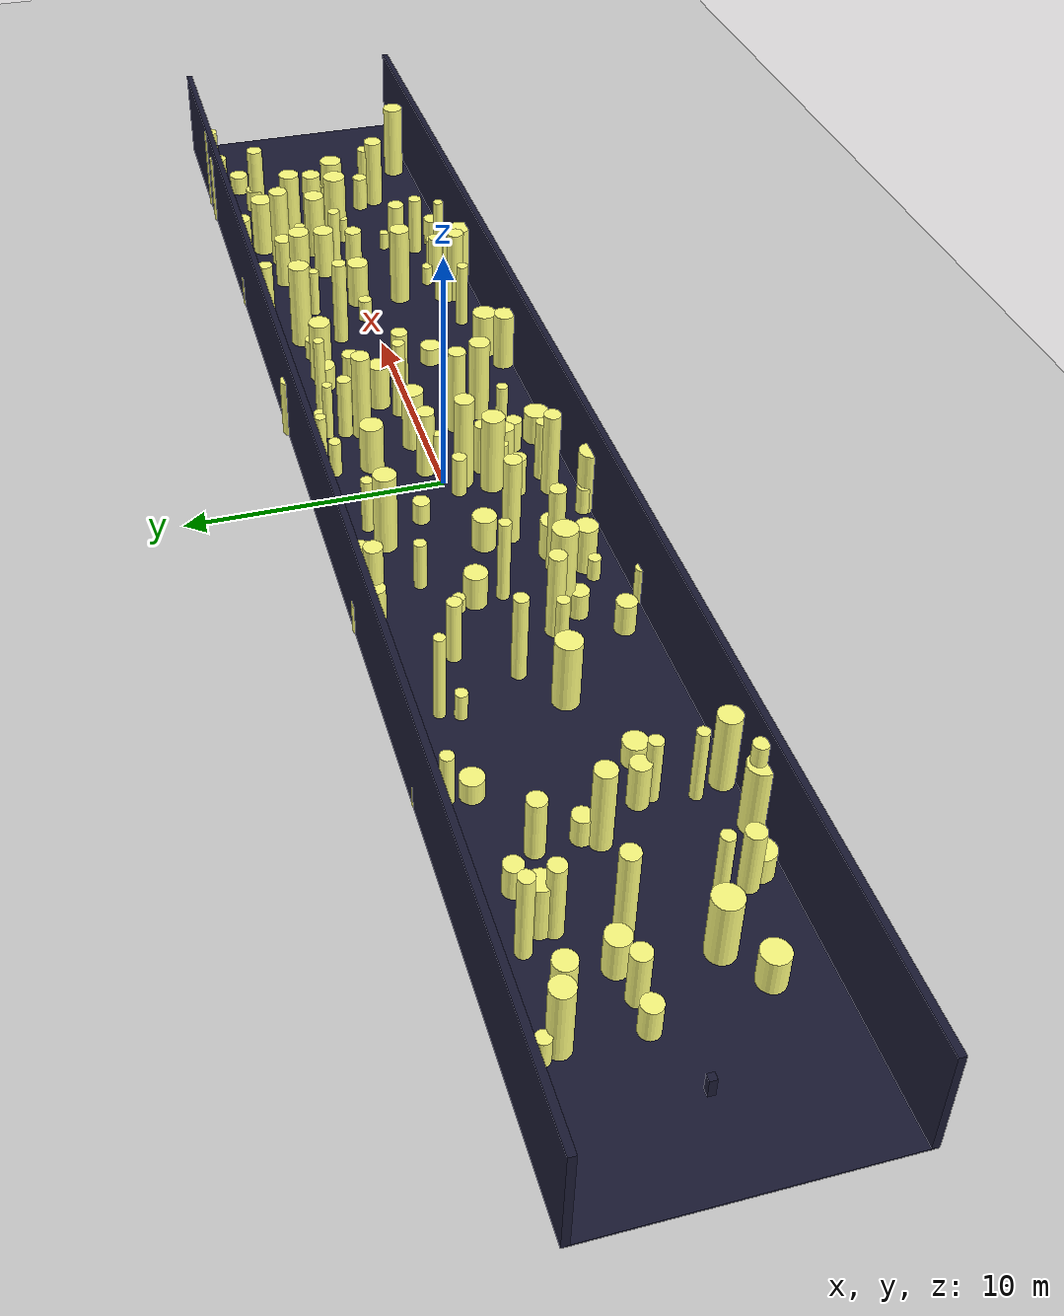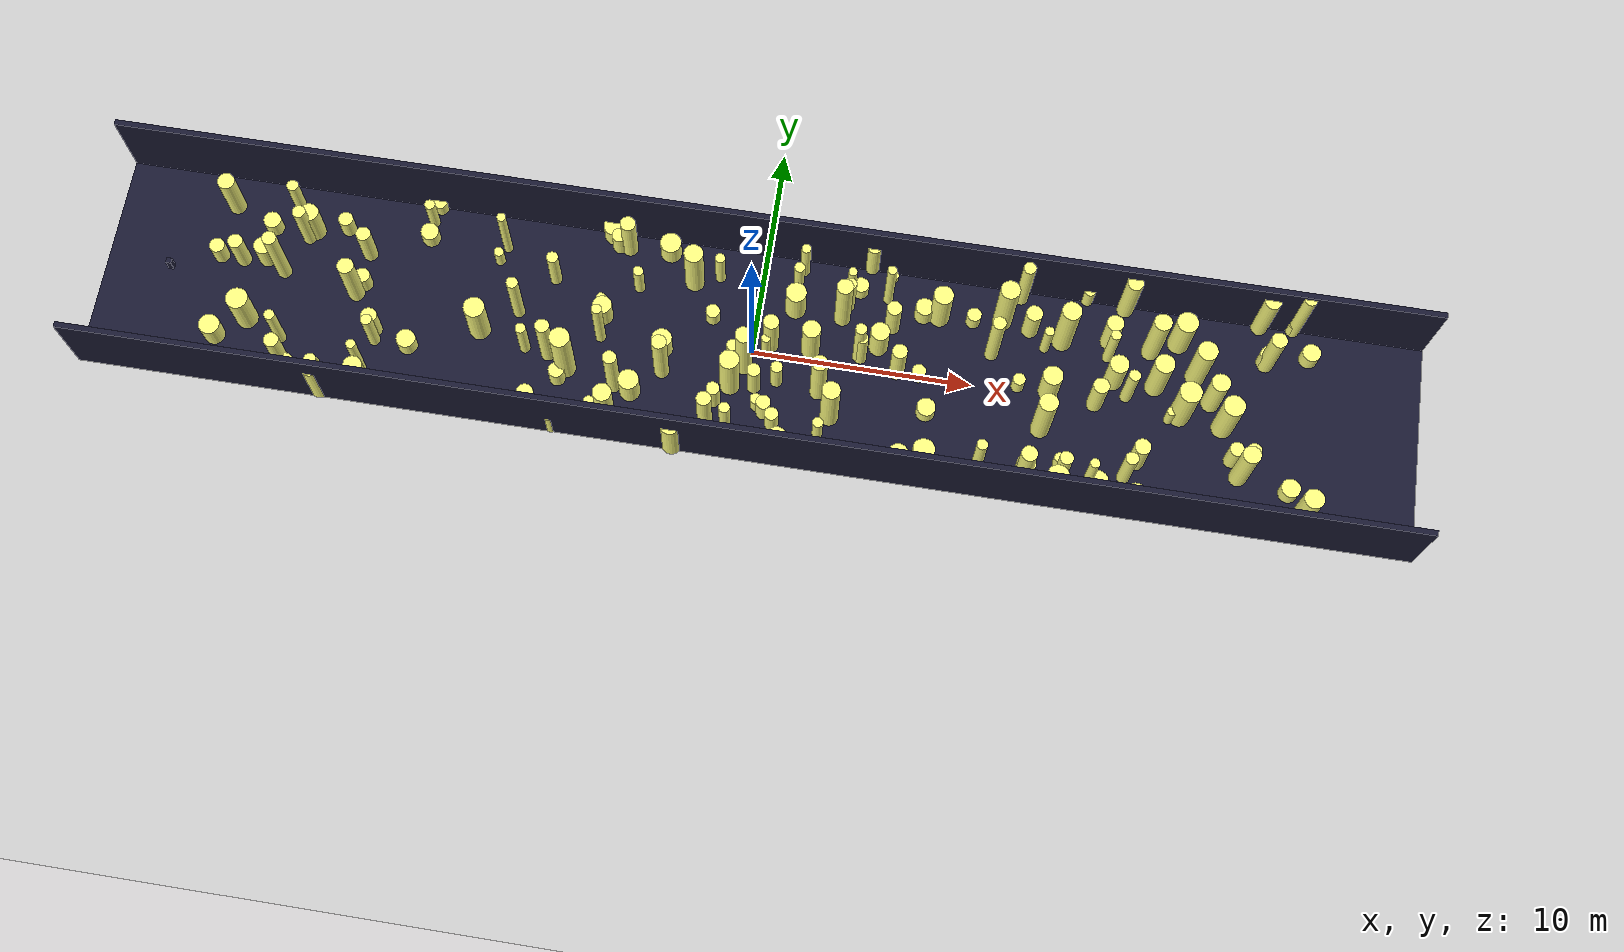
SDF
<?xml version="1.0"?>
<sdf version="1.4">
  <world name="default">
    <gui>
      <camera name="user_camera">
        <pose>-20 -30 40 0 0.66 0.83</pose>
      </camera>
    </gui>
    <include>
      <uri>model://ground_plane</uri>
    </include>
    <include>
      <uri>model://sun</uri>
    </include>
    <scene>
      <shadows>0</shadows>
    </scene>
    <model name="forest">
      <static>true</static>
      <link name="cylinder0">
        <pose>-23.785170255682715 0.858615654751226 1.0680569842711363 0 0 0 </pose>
        <visual name="visual">
          <geometry>
            <cylinder>
              <radius>0.3402988717110522</radius>
              <length>2.1361139685422725</length>
            </cylinder>
          </geometry>
          <material>
            <ambient>0.6 0.6 0.6 1</ambient>
            <diffuse>1 1 0.5 1</diffuse>
            <specular>0 0 0</specular>
            <emissive>0 0 0 1</emissive>
          </material>
        </visual>
        <collision name="collision">
          <geometry>
            <cylinder>
              <radius>0.3402988717110522</radius>
              <length>2.1361139685422725</length>
            </cylinder>
          </geometry>
          <max_contacts>0</max_contacts>
        </collision>
      </link>
      <link name="cylinder1">
        <pose>12.798375393576244 -3.2828685525187096 0.7205334273208008 0 0 0 </pose>
        <visual name="visual">
          <geometry>
            <cylinder>
              <radius>0.2074521253241624</radius>
              <length>1.4410668546416017</length>
            </cylinder>
          </geometry>
          <material>
            <ambient>0.6 0.6 0.6 1</ambient>
            <diffuse>1 1 0.5 1</diffuse>
            <specular>0 0 0</specular>
            <emissive>0 0 0 1</emissive>
          </material>
        </visual>
        <collision name="collision">
          <geometry>
            <cylinder>
              <radius>0.2074521253241624</radius>
              <length>1.4410668546416017</length>
            </cylinder>
          </geometry>
          <max_contacts>0</max_contacts>
        </collision>
      </link>
      <link name="cylinder2">
        <pose>-16.982513130498866 -4.464230554886309 1.5181779043415704 0 0 0 </pose>
        <visual name="visual">
          <geometry>
            <cylinder>
              <radius>0.41453890767657153</radius>
              <length>3.036355808683141</length>
            </cylinder>
          </geometry>
          <material>
            <ambient>0.6 0.6 0.6 1</ambient>
            <diffuse>1 1 0.5 1</diffuse>
            <specular>0 0 0</specular>
            <emissive>0 0 0 1</emissive>
          </material>
        </visual>
        <collision name="collision">
          <geometry>
            <cylinder>
              <radius>0.41453890767657153</radius>
              <length>3.036355808683141</length>
            </cylinder>
          </geometry>
          <max_contacts>0</max_contacts>
        </collision>
      </link>
      <link name="cylinder3">
        <pose>12.063372315469614 0.259676773497171 0.5206927669625371 0 0 0 </pose>
        <visual name="visual">
          <geometry>
            <cylinder>
              <radius>0.2870176923711316</radius>
              <length>1.0413855339250742</length>
            </cylinder>
          </geometry>
          <material>
            <ambient>0.6 0.6 0.6 1</ambient>
            <diffuse>1 1 0.5 1</diffuse>
            <specular>0 0 0</specular>
            <emissive>0 0 0 1</emissive>
          </material>
        </visual>
        <collision name="collision">
          <geometry>
            <cylinder>
              <radius>0.2870176923711316</radius>
              <length>1.0413855339250742</length>
            </cylinder>
          </geometry>
          <max_contacts>0</max_contacts>
        </collision>
      </link>
      <link name="cylinder4">
        <pose>-17.305909216532676 -3.473697885444673 1.4575486880233148 0 0 0 </pose>
        <visual name="visual">
          <geometry>
            <cylinder>
              <radius>0.21732607669334028</radius>
              <length>2.9150973760466297</length>
            </cylinder>
          </geometry>
          <material>
            <ambient>0.6 0.6 0.6 1</ambient>
            <diffuse>1 1 0.5 1</diffuse>
            <specular>0 0 0</specular>
            <emissive>0 0 0 1</emissive>
          </material>
        </visual>
        <collision name="collision">
          <geometry>
            <cylinder>
              <radius>0.21732607669334028</radius>
              <length>2.9150973760466297</length>
            </cylinder>
          </geometry>
          <max_contacts>0</max_contacts>
        </collision>
      </link>
      <link name="cylinder5">
        <pose>-4.4134026240362445 4.272519568705716 0.6251129250226404 0 0 0 </pose>
        <visual name="visual">
          <geometry>
            <cylinder>
              <radius>0.48298032674248287</radius>
              <length>1.2502258500452808</length>
            </cylinder>
          </geometry>
          <material>
            <ambient>0.6 0.6 0.6 1</ambient>
            <diffuse>1 1 0.5 1</diffuse>
            <specular>0 0 0</specular>
            <emissive>0 0 0 1</emissive>
          </material>
        </visual>
        <collision name="collision">
          <geometry>
            <cylinder>
              <radius>0.48298032674248287</radius>
              <length>1.2502258500452808</length>
            </cylinder>
          </geometry>
          <max_contacts>0</max_contacts>
        </collision>
      </link>
      <link name="cylinder6">
        <pose>4.462158580288072 3.7385799074985435 0.44079172515606957 0 0 0 </pose>
        <visual name="visual">
          <geometry>
            <cylinder>
              <radius>0.3588167858036847</radius>
              <length>0.8815834503121391</length>
            </cylinder>
          </geometry>
          <material>
            <ambient>0.6 0.6 0.6 1</ambient>
            <diffuse>1 1 0.5 1</diffuse>
            <specular>0 0 0</specular>
            <emissive>0 0 0 1</emissive>
          </material>
        </visual>
        <collision name="collision">
          <geometry>
            <cylinder>
              <radius>0.3588167858036847</radius>
              <length>0.8815834503121391</length>
            </cylinder>
          </geometry>
          <max_contacts>0</max_contacts>
        </collision>
      </link>
      <link name="cylinder7">
        <pose>-21.497163602215124 3.442455883583156 1.6812864613903267 0 0 0 </pose>
        <visual name="visual">
          <geometry>
            <cylinder>
              <radius>0.2655494989353468</radius>
              <length>3.3625729227806533</length>
            </cylinder>
          </geometry>
          <material>
            <ambient>0.6 0.6 0.6 1</ambient>
            <diffuse>1 1 0.5 1</diffuse>
            <specular>0 0 0</specular>
            <emissive>0 0 0 1</emissive>
          </material>
        </visual>
        <collision name="collision">
          <geometry>
            <cylinder>
              <radius>0.2655494989353468</radius>
              <length>3.3625729227806533</length>
            </cylinder>
          </geometry>
          <max_contacts>0</max_contacts>
        </collision>
      </link>
      <link name="cylinder8">
        <pose>4.90252276802174 0.48921091091704927 1.2853089699839402 0 0 0 </pose>
        <visual name="visual">
          <geometry>
            <cylinder>
              <radius>0.2614693026425224</radius>
              <length>2.5706179399678803</length>
            </cylinder>
          </geometry>
          <material>
            <ambient>0.6 0.6 0.6 1</ambient>
            <diffuse>1 1 0.5 1</diffuse>
            <specular>0 0 0</specular>
            <emissive>0 0 0 1</emissive>
          </material>
        </visual>
        <collision name="collision">
          <geometry>
            <cylinder>
              <radius>0.2614693026425224</radius>
              <length>2.5706179399678803</length>
            </cylinder>
          </geometry>
          <max_contacts>0</max_contacts>
        </collision>
      </link>
      <link name="cylinder9">
        <pose>16.92552058372282 0.5468688813929665 1.3953429441775678 0 0 0 </pose>
        <visual name="visual">
          <geometry>
            <cylinder>
              <radius>0.26180924563030633</radius>
              <length>2.7906858883551355</length>
            </cylinder>
          </geometry>
          <material>
            <ambient>0.6 0.6 0.6 1</ambient>
            <diffuse>1 1 0.5 1</diffuse>
            <specular>0 0 0</specular>
            <emissive>0 0 0 1</emissive>
          </material>
        </visual>
        <collision name="collision">
          <geometry>
            <cylinder>
              <radius>0.26180924563030633</radius>
              <length>2.7906858883551355</length>
            </cylinder>
          </geometry>
          <max_contacts>0</max_contacts>
        </collision>
      </link>
      <link name="cylinder10">
        <pose>0.35884433154932793 -1.6306497201837198 1.1159105243746459 0 0 0 </pose>
        <visual name="visual">
          <geometry>
            <cylinder>
              <radius>0.30563387176221746</radius>
              <length>2.2318210487492918</length>
            </cylinder>
          </geometry>
          <material>
            <ambient>0.6 0.6 0.6 1</ambient>
            <diffuse>1 1 0.5 1</diffuse>
            <specular>0 0 0</specular>
            <emissive>0 0 0 1</emissive>
          </material>
        </visual>
        <collision name="collision">
          <geometry>
            <cylinder>
              <radius>0.30563387176221746</radius>
              <length>2.2318210487492918</length>
            </cylinder>
          </geometry>
          <max_contacts>0</max_contacts>
        </collision>
      </link>
      <link name="cylinder11">
        <pose>3.237439862645047 -1.4215264279106354 1.868700355015458 0 0 0 </pose>
        <visual name="visual">
          <geometry>
            <cylinder>
              <radius>0.36327619562679125</radius>
              <length>3.737400710030916</length>
            </cylinder>
          </geometry>
          <material>
            <ambient>0.6 0.6 0.6 1</ambient>
            <diffuse>1 1 0.5 1</diffuse>
            <specular>0 0 0</specular>
            <emissive>0 0 0 1</emissive>
          </material>
        </visual>
        <collision name="collision">
          <geometry>
            <cylinder>
              <radius>0.36327619562679125</radius>
              <length>3.737400710030916</length>
            </cylinder>
          </geometry>
          <max_contacts>0</max_contacts>
        </collision>
      </link>
      <link name="cylinder12">
        <pose>2.612873712708769 0.5241438222223884 1.3351725123235476 0 0 0 </pose>
        <visual name="visual">
          <geometry>
            <cylinder>
              <radius>0.4195239390437968</radius>
              <length>2.6703450246470952</length>
            </cylinder>
          </geometry>
          <material>
            <ambient>0.6 0.6 0.6 1</ambient>
            <diffuse>1 1 0.5 1</diffuse>
            <specular>0 0 0</specular>
            <emissive>0 0 0 1</emissive>
          </material>
        </visual>
        <collision name="collision">
          <geometry>
            <cylinder>
              <radius>0.4195239390437968</radius>
              <length>2.6703450246470952</length>
            </cylinder>
          </geometry>
          <max_contacts>0</max_contacts>
        </collision>
      </link>
      <link name="cylinder13">
        <pose>21.8047754650202 -1.7430730146435627 0.8334987781587296 0 0 0 </pose>
        <visual name="visual">
          <geometry>
            <cylinder>
              <radius>0.327413833274928</radius>
              <length>1.6669975563174593</length>
            </cylinder>
          </geometry>
          <material>
            <ambient>0.6 0.6 0.6 1</ambient>
            <diffuse>1 1 0.5 1</diffuse>
            <specular>0 0 0</specular>
            <emissive>0 0 0 1</emissive>
          </material>
        </visual>
        <collision name="collision">
          <geometry>
            <cylinder>
              <radius>0.327413833274928</radius>
              <length>1.6669975563174593</length>
            </cylinder>
          </geometry>
          <max_contacts>0</max_contacts>
        </collision>
      </link>
      <link name="cylinder14">
        <pose>-15.424550456200043 -2.119455929859245 0.4834123405492821 0 0 0 </pose>
        <visual name="visual">
          <geometry>
            <cylinder>
              <radius>0.43687664144653027</radius>
              <length>0.9668246810985642</length>
            </cylinder>
          </geometry>
          <material>
            <ambient>0.6 0.6 0.6 1</ambient>
            <diffuse>1 1 0.5 1</diffuse>
            <specular>0 0 0</specular>
            <emissive>0 0 0 1</emissive>
          </material>
        </visual>
        <collision name="collision">
          <geometry>
            <cylinder>
              <radius>0.43687664144653027</radius>
              <length>0.9668246810985642</length>
            </cylinder>
          </geometry>
          <max_contacts>0</max_contacts>
        </collision>
      </link>
      <link name="cylinder15">
        <pose>-24.830451484869965 0.8806531129328423 0.6390781866645068 0 0 0 </pose>
        <visual name="visual">
          <geometry>
            <cylinder>
              <radius>0.35179560158539624</radius>
              <length>1.2781563733290136</length>
            </cylinder>
          </geometry>
          <material>
            <ambient>0.6 0.6 0.6 1</ambient>
            <diffuse>1 1 0.5 1</diffuse>
            <specular>0 0 0</specular>
            <emissive>0 0 0 1</emissive>
          </material>
        </visual>
        <collision name="collision">
          <geometry>
            <cylinder>
              <radius>0.35179560158539624</radius>
              <length>1.2781563733290136</length>
            </cylinder>
          </geometry>
          <max_contacts>0</max_contacts>
        </collision>
      </link>
      <link name="cylinder16">
        <pose>-17.09226629540975 -1.618599905884798 0.9177513465718122 0 0 0 </pose>
        <visual name="visual">
          <geometry>
            <cylinder>
              <radius>0.36407450608267056</radius>
              <length>1.8355026931436245</length>
            </cylinder>
          </geometry>
          <material>
            <ambient>0.6 0.6 0.6 1</ambient>
            <diffuse>1 1 0.5 1</diffuse>
            <specular>0 0 0</specular>
            <emissive>0 0 0 1</emissive>
          </material>
        </visual>
        <collision name="collision">
          <geometry>
            <cylinder>
              <radius>0.36407450608267056</radius>
              <length>1.8355026931436245</length>
            </cylinder>
          </geometry>
          <max_contacts>0</max_contacts>
        </collision>
      </link>
      <link name="cylinder17">
        <pose>15.560407921322614 -0.032807102858358306 1.2310892919635181 0 0 0 </pose>
        <visual name="visual">
          <geometry>
            <cylinder>
              <radius>0.3613761600537685</radius>
              <length>2.4621785839270363</length>
            </cylinder>
          </geometry>
          <material>
            <ambient>0.6 0.6 0.6 1</ambient>
            <diffuse>1 1 0.5 1</diffuse>
            <specular>0 0 0</specular>
            <emissive>0 0 0 1</emissive>
          </material>
        </visual>
        <collision name="collision">
          <geometry>
            <cylinder>
              <radius>0.3613761600537685</radius>
              <length>2.4621785839270363</length>
            </cylinder>
          </geometry>
          <max_contacts>0</max_contacts>
        </collision>
      </link>
      <link name="cylinder18">
        <pose>5.761139175603063 3.538941274273853 1.7364097716783282 0 0 0 </pose>
        <visual name="visual">
          <geometry>
            <cylinder>
              <radius>0.2109118705974057</radius>
              <length>3.4728195433566564</length>
            </cylinder>
          </geometry>
          <material>
            <ambient>0.6 0.6 0.6 1</ambient>
            <diffuse>1 1 0.5 1</diffuse>
            <specular>0 0 0</specular>
            <emissive>0 0 0 1</emissive>
          </material>
        </visual>
        <collision name="collision">
          <geometry>
            <cylinder>
              <radius>0.2109118705974057</radius>
              <length>3.4728195433566564</length>
            </cylinder>
          </geometry>
          <max_contacts>0</max_contacts>
        </collision>
      </link>
      <link name="cylinder19">
        <pose>18.150752491414572 1.2028664458033589 1.512272726877565 0 0 0 </pose>
        <visual name="visual">
          <geometry>
            <cylinder>
              <radius>0.44529768430421035</radius>
              <length>3.02454545375513</length>
            </cylinder>
          </geometry>
          <material>
            <ambient>0.6 0.6 0.6 1</ambient>
            <diffuse>1 1 0.5 1</diffuse>
            <specular>0 0 0</specular>
            <emissive>0 0 0 1</emissive>
          </material>
        </visual>
        <collision name="collision">
          <geometry>
            <cylinder>
              <radius>0.44529768430421035</radius>
              <length>3.02454545375513</length>
            </cylinder>
          </geometry>
          <max_contacts>0</max_contacts>
        </collision>
      </link>
      <link name="cylinder20">
        <pose>-7.146554907595238 1.3591154046007201 0.32350330603252303 0 0 0 </pose>
        <visual name="visual">
          <geometry>
            <cylinder>
              <radius>0.2321273657846676</radius>
              <length>0.6470066120650461</length>
            </cylinder>
          </geometry>
          <material>
            <ambient>0.6 0.6 0.6 1</ambient>
            <diffuse>1 1 0.5 1</diffuse>
            <specular>0 0 0</specular>
            <emissive>0 0 0 1</emissive>
          </material>
        </visual>
        <collision name="collision">
          <geometry>
            <cylinder>
              <radius>0.2321273657846676</radius>
              <length>0.6470066120650461</length>
            </cylinder>
          </geometry>
          <max_contacts>0</max_contacts>
        </collision>
      </link>
      <link name="cylinder21">
        <pose>-0.7801931591326259 -0.42378372629529437 0.8790911549478188 0 0 0 </pose>
        <visual name="visual">
          <geometry>
            <cylinder>
              <radius>0.27697668428740363</radius>
              <length>1.7581823098956375</length>
            </cylinder>
          </geometry>
          <material>
            <ambient>0.6 0.6 0.6 1</ambient>
            <diffuse>1 1 0.5 1</diffuse>
            <specular>0 0 0</specular>
            <emissive>0 0 0 1</emissive>
          </material>
        </visual>
        <collision name="collision">
          <geometry>
            <cylinder>
              <radius>0.27697668428740363</radius>
              <length>1.7581823098956375</length>
            </cylinder>
          </geometry>
          <max_contacts>0</max_contacts>
        </collision>
      </link>
      <link name="cylinder22">
        <pose>-6.776622383678561 4.212827206988498 0.7084860347944146 0 0 0 </pose>
        <visual name="visual">
          <geometry>
            <cylinder>
              <radius>0.3408848058256867</radius>
              <length>1.4169720695888293</length>
            </cylinder>
          </geometry>
          <material>
            <ambient>0.6 0.6 0.6 1</ambient>
            <diffuse>1 1 0.5 1</diffuse>
            <specular>0 0 0</specular>
            <emissive>0 0 0 1</emissive>
          </material>
        </visual>
        <collision name="collision">
          <geometry>
            <cylinder>
              <radius>0.3408848058256867</radius>
              <length>1.4169720695888293</length>
            </cylinder>
          </geometry>
          <max_contacts>0</max_contacts>
        </collision>
      </link>
      <link name="cylinder23">
        <pose>14.741480302558436 4.915428209651903 0.6339529873361176 0 0 0 </pose>
        <visual name="visual">
          <geometry>
            <cylinder>
              <radius>0.25261547616194646</radius>
              <length>1.2679059746722352</length>
            </cylinder>
          </geometry>
          <material>
            <ambient>0.6 0.6 0.6 1</ambient>
            <diffuse>1 1 0.5 1</diffuse>
            <specular>0 0 0</specular>
            <emissive>0 0 0 1</emissive>
          </material>
        </visual>
        <collision name="collision">
          <geometry>
            <cylinder>
              <radius>0.25261547616194646</radius>
              <length>1.2679059746722352</length>
            </cylinder>
          </geometry>
          <max_contacts>0</max_contacts>
        </collision>
      </link>
      <link name="cylinder24">
        <pose>-3.018274304357611 -4.616674828413324 0.6000016276231543 0 0 0 </pose>
        <visual name="visual">
          <geometry>
            <cylinder>
              <radius>0.27451290789629884</radius>
              <length>1.2000032552463087</length>
            </cylinder>
          </geometry>
          <material>
            <ambient>0.6 0.6 0.6 1</ambient>
            <diffuse>1 1 0.5 1</diffuse>
            <specular>0 0 0</specular>
            <emissive>0 0 0 1</emissive>
          </material>
        </visual>
        <collision name="collision">
          <geometry>
            <cylinder>
              <radius>0.27451290789629884</radius>
              <length>1.2000032552463087</length>
            </cylinder>
          </geometry>
          <max_contacts>0</max_contacts>
        </collision>
      </link>
      <link name="cylinder25">
        <pose>-12.109198337162896 2.655638317493475 0.5547450570341494 0 0 0 </pose>
        <visual name="visual">
          <geometry>
            <cylinder>
              <radius>0.2238756173687885</radius>
              <length>1.109490114068299</length>
            </cylinder>
          </geometry>
          <material>
            <ambient>0.6 0.6 0.6 1</ambient>
            <diffuse>1 1 0.5 1</diffuse>
            <specular>0 0 0</specular>
            <emissive>0 0 0 1</emissive>
          </material>
        </visual>
        <collision name="collision">
          <geometry>
            <cylinder>
              <radius>0.2238756173687885</radius>
              <length>1.109490114068299</length>
            </cylinder>
          </geometry>
          <max_contacts>0</max_contacts>
        </collision>
      </link>
      <link name="cylinder26">
        <pose>-1.5002499025637057 -3.789375244378266 1.7986329762283029 0 0 0 </pose>
        <visual name="visual">
          <geometry>
            <cylinder>
              <radius>0.3321129033527981</radius>
              <length>3.5972659524566057</length>
            </cylinder>
          </geometry>
          <material>
            <ambient>0.6 0.6 0.6 1</ambient>
            <diffuse>1 1 0.5 1</diffuse>
            <specular>0 0 0</specular>
            <emissive>0 0 0 1</emissive>
          </material>
        </visual>
        <collision name="collision">
          <geometry>
            <cylinder>
              <radius>0.3321129033527981</radius>
              <length>3.5972659524566057</length>
            </cylinder>
          </geometry>
          <max_contacts>0</max_contacts>
        </collision>
      </link>
      <link name="cylinder27">
        <pose>-15.336848639112066 4.816204754179994 0.39421610292568143 0 0 0 </pose>
        <visual name="visual">
          <geometry>
            <cylinder>
              <radius>0.3200530086702805</radius>
              <length>0.7884322058513629</length>
            </cylinder>
          </geometry>
          <material>
            <ambient>0.6 0.6 0.6 1</ambient>
            <diffuse>1 1 0.5 1</diffuse>
            <specular>0 0 0</specular>
            <emissive>0 0 0 1</emissive>
          </material>
        </visual>
        <collision name="collision">
          <geometry>
            <cylinder>
              <radius>0.3200530086702805</radius>
              <length>0.7884322058513629</length>
            </cylinder>
          </geometry>
          <max_contacts>0</max_contacts>
        </collision>
      </link>
      <link name="cylinder28">
        <pose>1.324380870334501 -1.2024983633252875 0.9479656830783172 0 0 0 </pose>
        <visual name="visual">
          <geometry>
            <cylinder>
              <radius>0.2684165660967434</radius>
              <length>1.8959313661566344</length>
            </cylinder>
          </geometry>
          <material>
            <ambient>0.6 0.6 0.6 1</ambient>
            <diffuse>1 1 0.5 1</diffuse>
            <specular>0 0 0</specular>
            <emissive>0 0 0 1</emissive>
          </material>
        </visual>
        <collision name="collision">
          <geometry>
            <cylinder>
              <radius>0.2684165660967434</radius>
              <length>1.8959313661566344</length>
            </cylinder>
          </geometry>
          <max_contacts>0</max_contacts>
        </collision>
      </link>
      <link name="cylinder29">
        <pose>-24.719279816919176 3.440128337403527 1.3865433847531825 0 0 0 </pose>
        <visual name="visual">
          <geometry>
            <cylinder>
              <radius>0.3936484266282352</radius>
              <length>2.773086769506365</length>
            </cylinder>
          </geometry>
          <material>
            <ambient>0.6 0.6 0.6 1</ambient>
            <diffuse>1 1 0.5 1</diffuse>
            <specular>0 0 0</specular>
            <emissive>0 0 0 1</emissive>
          </material>
        </visual>
        <collision name="collision">
          <geometry>
            <cylinder>
              <radius>0.3936484266282352</radius>
              <length>2.773086769506365</length>
            </cylinder>
          </geometry>
          <max_contacts>0</max_contacts>
        </collision>
      </link>
      <link name="cylinder30">
        <pose>8.130976952824462 -1.6403841777668173 0.4284824671894183 0 0 0 </pose>
        <visual name="visual">
          <geometry>
            <cylinder>
              <radius>0.42356399673454814</radius>
              <length>0.8569649343788366</length>
            </cylinder>
          </geometry>
          <material>
            <ambient>0.6 0.6 0.6 1</ambient>
            <diffuse>1 1 0.5 1</diffuse>
            <specular>0 0 0</specular>
            <emissive>0 0 0 1</emissive>
          </material>
        </visual>
        <collision name="collision">
          <geometry>
            <cylinder>
              <radius>0.42356399673454814</radius>
              <length>0.8569649343788366</length>
            </cylinder>
          </geometry>
          <max_contacts>0</max_contacts>
        </collision>
      </link>
      <link name="cylinder31">
        <pose>13.062057646591683 2.2853198517324413 1.0914935900410399 0 0 0 </pose>
        <visual name="visual">
          <geometry>
            <cylinder>
              <radius>0.2118241215187681</radius>
              <length>2.1829871800820797</length>
            </cylinder>
          </geometry>
          <material>
            <ambient>0.6 0.6 0.6 1</ambient>
            <diffuse>1 1 0.5 1</diffuse>
            <specular>0 0 0</specular>
            <emissive>0 0 0 1</emissive>
          </material>
        </visual>
        <collision name="collision">
          <geometry>
            <cylinder>
              <radius>0.2118241215187681</radius>
              <length>2.1829871800820797</length>
            </cylinder>
          </geometry>
          <max_contacts>0</max_contacts>
        </collision>
      </link>
      <link name="cylinder32">
        <pose>-12.344993057159408 -0.8581550215634417 1.3897939412623308 0 0 0 </pose>
        <visual name="visual">
          <geometry>
            <cylinder>
              <radius>0.47974164405565967</radius>
              <length>2.7795878825246616</length>
            </cylinder>
          </geometry>
          <material>
            <ambient>0.6 0.6 0.6 1</ambient>
            <diffuse>1 1 0.5 1</diffuse>
            <specular>0 0 0</specular>
            <emissive>0 0 0 1</emissive>
          </material>
        </visual>
        <collision name="collision">
          <geometry>
            <cylinder>
              <radius>0.47974164405565967</radius>
              <length>2.7795878825246616</length>
            </cylinder>
          </geometry>
          <max_contacts>0</max_contacts>
        </collision>
      </link>
      <link name="cylinder33">
        <pose>4.006814596763224 2.9329232268723757 1.344608304612453 0 0 0 </pose>
        <visual name="visual">
          <geometry>
            <cylinder>
              <radius>0.28467719946347414</radius>
              <length>2.689216609224906</length>
            </cylinder>
          </geometry>
          <material>
            <ambient>0.6 0.6 0.6 1</ambient>
            <diffuse>1 1 0.5 1</diffuse>
            <specular>0 0 0</specular>
            <emissive>0 0 0 1</emissive>
          </material>
        </visual>
        <collision name="collision">
          <geometry>
            <cylinder>
              <radius>0.28467719946347414</radius>
              <length>2.689216609224906</length>
            </cylinder>
          </geometry>
          <max_contacts>0</max_contacts>
        </collision>
      </link>
      <link name="cylinder34">
        <pose>15.546510192347114 -3.9565848857622 1.6730990246546018 0 0 0 </pose>
        <visual name="visual">
          <geometry>
            <cylinder>
              <radius>0.21259409692973114</radius>
              <length>3.3461980493092036</length>
            </cylinder>
          </geometry>
          <material>
            <ambient>0.6 0.6 0.6 1</ambient>
            <diffuse>1 1 0.5 1</diffuse>
            <specular>0 0 0</specular>
            <emissive>0 0 0 1</emissive>
          </material>
        </visual>
        <collision name="collision">
          <geometry>
            <cylinder>
              <radius>0.21259409692973114</radius>
              <length>3.3461980493092036</length>
            </cylinder>
          </geometry>
          <max_contacts>0</max_contacts>
        </collision>
      </link>
      <link name="cylinder35">
        <pose>7.598558792869461 0.04883102754331148 0.3924039694887407 0 0 0 </pose>
        <visual name="visual">
          <geometry>
            <cylinder>
              <radius>0.3150307945010926</radius>
              <length>0.7848079389774814</length>
            </cylinder>
          </geometry>
          <material>
            <ambient>0.6 0.6 0.6 1</ambient>
            <diffuse>1 1 0.5 1</diffuse>
            <specular>0 0 0</specular>
            <emissive>0 0 0 1</emissive>
          </material>
        </visual>
        <collision name="collision">
          <geometry>
            <cylinder>
              <radius>0.3150307945010926</radius>
              <length>0.7848079389774814</length>
            </cylinder>
          </geometry>
          <max_contacts>0</max_contacts>
        </collision>
      </link>
      <link name="cylinder36">
        <pose>-1.3245627317411923 -2.574910769122596 0.862850663219632 0 0 0 </pose>
        <visual name="visual">
          <geometry>
            <cylinder>
              <radius>0.305779836264553</radius>
              <length>1.725701326439264</length>
            </cylinder>
          </geometry>
          <material>
            <ambient>0.6 0.6 0.6 1</ambient>
            <diffuse>1 1 0.5 1</diffuse>
            <specular>0 0 0</specular>
            <emissive>0 0 0 1</emissive>
          </material>
        </visual>
        <collision name="collision">
          <geometry>
            <cylinder>
              <radius>0.305779836264553</radius>
              <length>1.725701326439264</length>
            </cylinder>
          </geometry>
          <max_contacts>0</max_contacts>
        </collision>
      </link>
      <link name="cylinder37">
        <pose>13.803841783484906 2.719741079920097 1.8922707779875454 0 0 0 </pose>
        <visual name="visual">
          <geometry>
            <cylinder>
              <radius>0.4399418925004805</radius>
              <length>3.784541555975091</length>
            </cylinder>
          </geometry>
          <material>
            <ambient>0.6 0.6 0.6 1</ambient>
            <diffuse>1 1 0.5 1</diffuse>
            <specular>0 0 0</specular>
            <emissive>0 0 0 1</emissive>
          </material>
        </visual>
        <collision name="collision">
          <geometry>
            <cylinder>
              <radius>0.4399418925004805</radius>
              <length>3.784541555975091</length>
            </cylinder>
          </geometry>
          <max_contacts>0</max_contacts>
        </collision>
      </link>
      <link name="cylinder38">
        <pose>-10.767923466901912 0.28126110510569546 1.75378816546496 0 0 0 </pose>
        <visual name="visual">
          <geometry>
            <cylinder>
              <radius>0.26946038249747256</radius>
              <length>3.50757633092992</length>
            </cylinder>
          </geometry>
          <material>
            <ambient>0.6 0.6 0.6 1</ambient>
            <diffuse>1 1 0.5 1</diffuse>
            <specular>0 0 0</specular>
            <emissive>0 0 0 1</emissive>
          </material>
        </visual>
        <collision name="collision">
          <geometry>
            <cylinder>
              <radius>0.26946038249747256</radius>
              <length>3.50757633092992</length>
            </cylinder>
          </geometry>
          <max_contacts>0</max_contacts>
        </collision>
      </link>
      <link name="cylinder39">
        <pose>-5.542187458005763 2.330024956682271 1.0112195197869174 0 0 0 </pose>
        <visual name="visual">
          <geometry>
            <cylinder>
              <radius>0.2346234141529287</radius>
              <length>2.0224390395738348</length>
            </cylinder>
          </geometry>
          <material>
            <ambient>0.6 0.6 0.6 1</ambient>
            <diffuse>1 1 0.5 1</diffuse>
            <specular>0 0 0</specular>
            <emissive>0 0 0 1</emissive>
          </material>
        </visual>
        <collision name="collision">
          <geometry>
            <cylinder>
              <radius>0.2346234141529287</radius>
              <length>2.0224390395738348</length>
            </cylinder>
          </geometry>
          <max_contacts>0</max_contacts>
        </collision>
      </link>
      <link name="cylinder40">
        <pose>-21.79514124067716 0.5589695124922365 1.9137921319072406 0 0 0 </pose>
        <visual name="visual">
          <geometry>
            <cylinder>
              <radius>0.325509300702765</radius>
              <length>3.8275842638144812</length>
            </cylinder>
          </geometry>
          <material>
            <ambient>0.6 0.6 0.6 1</ambient>
            <diffuse>1 1 0.5 1</diffuse>
            <specular>0 0 0</specular>
            <emissive>0 0 0 1</emissive>
          </material>
        </visual>
        <collision name="collision">
          <geometry>
            <cylinder>
              <radius>0.325509300702765</radius>
              <length>3.8275842638144812</length>
            </cylinder>
          </geometry>
          <max_contacts>0</max_contacts>
        </collision>
      </link>
      <link name="cylinder41">
        <pose>-6.868907569636146 -0.3416063995372749 1.7190181544570673 0 0 0 </pose>
        <visual name="visual">
          <geometry>
            <cylinder>
              <radius>0.23068241252803065</radius>
              <length>3.4380363089141346</length>
            </cylinder>
          </geometry>
          <material>
            <ambient>0.6 0.6 0.6 1</ambient>
            <diffuse>1 1 0.5 1</diffuse>
            <specular>0 0 0</specular>
            <emissive>0 0 0 1</emissive>
          </material>
        </visual>
        <collision name="collision">
          <geometry>
            <cylinder>
              <radius>0.23068241252803065</radius>
              <length>3.4380363089141346</length>
            </cylinder>
          </geometry>
          <max_contacts>0</max_contacts>
        </collision>
      </link>
      <link name="cylinder42">
        <pose>-22.688539557558652 1.092514639524965 0.7696702428925606 0 0 0 </pose>
        <visual name="visual">
          <geometry>
            <cylinder>
              <radius>0.4211997071474807</radius>
              <length>1.5393404857851212</length>
            </cylinder>
          </geometry>
          <material>
            <ambient>0.6 0.6 0.6 1</ambient>
            <diffuse>1 1 0.5 1</diffuse>
            <specular>0 0 0</specular>
            <emissive>0 0 0 1</emissive>
          </material>
        </visual>
        <collision name="collision">
          <geometry>
            <cylinder>
              <radius>0.4211997071474807</radius>
              <length>1.5393404857851212</length>
            </cylinder>
          </geometry>
          <max_contacts>0</max_contacts>
        </collision>
      </link>
      <link name="cylinder43">
        <pose>-2.8140881032985554 -4.883507203454016 1.3338616905762894 0 0 0 </pose>
        <visual name="visual">
          <geometry>
            <cylinder>
              <radius>0.4538561000798747</radius>
              <length>2.667723381152579</length>
            </cylinder>
          </geometry>
          <material>
            <ambient>0.6 0.6 0.6 1</ambient>
            <diffuse>1 1 0.5 1</diffuse>
            <specular>0 0 0</specular>
            <emissive>0 0 0 1</emissive>
          </material>
        </visual>
        <collision name="collision">
          <geometry>
            <cylinder>
              <radius>0.4538561000798747</radius>
              <length>2.667723381152579</length>
            </cylinder>
          </geometry>
          <max_contacts>0</max_contacts>
        </collision>
      </link>
      <link name="cylinder44">
        <pose>-6.732094830644947 -3.7667867439288116 0.4926059050593634 0 0 0 </pose>
        <visual name="visual">
          <geometry>
            <cylinder>
              <radius>0.23911900259635044</radius>
              <length>0.9852118101187268</length>
            </cylinder>
          </geometry>
          <material>
            <ambient>0.6 0.6 0.6 1</ambient>
            <diffuse>1 1 0.5 1</diffuse>
            <specular>0 0 0</specular>
            <emissive>0 0 0 1</emissive>
          </material>
        </visual>
        <collision name="collision">
          <geometry>
            <cylinder>
              <radius>0.23911900259635044</radius>
              <length>0.9852118101187268</length>
            </cylinder>
          </geometry>
          <max_contacts>0</max_contacts>
        </collision>
      </link>
      <link name="cylinder45">
        <pose>-18.29430755576153 0.005436097848785515 1.6315916997252689 0 0 0 </pose>
        <visual name="visual">
          <geometry>
            <cylinder>
              <radius>0.37604112075896046</radius>
              <length>3.2631833994505377</length>
            </cylinder>
          </geometry>
          <material>
            <ambient>0.6 0.6 0.6 1</ambient>
            <diffuse>1 1 0.5 1</diffuse>
            <specular>0 0 0</specular>
            <emissive>0 0 0 1</emissive>
          </material>
        </visual>
        <collision name="collision">
          <geometry>
            <cylinder>
              <radius>0.37604112075896046</radius>
              <length>3.2631833994505377</length>
            </cylinder>
          </geometry>
          <max_contacts>0</max_contacts>
        </collision>
      </link>
      <link name="cylinder46">
        <pose>4.0363057467295 3.6115315765122453 1.266204614728753 0 0 0 </pose>
        <visual name="visual">
          <geometry>
            <cylinder>
              <radius>0.2000358598801799</radius>
              <length>2.532409229457506</length>
            </cylinder>
          </geometry>
          <material>
            <ambient>0.6 0.6 0.6 1</ambient>
            <diffuse>1 1 0.5 1</diffuse>
            <specular>0 0 0</specular>
            <emissive>0 0 0 1</emissive>
          </material>
        </visual>
        <collision name="collision">
          <geometry>
            <cylinder>
              <radius>0.2000358598801799</radius>
              <length>2.532409229457506</length>
            </cylinder>
          </geometry>
          <max_contacts>0</max_contacts>
        </collision>
      </link>
      <link name="cylinder47">
        <pose>-22.724056565020206 2.6316526298070873 0.5052599635196058 0 0 0 </pose>
        <visual name="visual">
          <geometry>
            <cylinder>
              <radius>0.3982028571683419</radius>
              <length>1.0105199270392116</length>
            </cylinder>
          </geometry>
          <material>
            <ambient>0.6 0.6 0.6 1</ambient>
            <diffuse>1 1 0.5 1</diffuse>
            <specular>0 0 0</specular>
            <emissive>0 0 0 1</emissive>
          </material>
        </visual>
        <collision name="collision">
          <geometry>
            <cylinder>
              <radius>0.3982028571683419</radius>
              <length>1.0105199270392116</length>
            </cylinder>
          </geometry>
          <max_contacts>0</max_contacts>
        </collision>
      </link>
      <link name="cylinder48">
        <pose>3.4940067916993947 -3.376209781901729 0.7850246277640844 0 0 0 </pose>
        <visual name="visual">
          <geometry>
            <cylinder>
              <radius>0.23609696893940707</radius>
              <length>1.5700492555281689</length>
            </cylinder>
          </geometry>
          <material>
            <ambient>0.6 0.6 0.6 1</ambient>
            <diffuse>1 1 0.5 1</diffuse>
            <specular>0 0 0</specular>
            <emissive>0 0 0 1</emissive>
          </material>
        </visual>
        <collision name="collision">
          <geometry>
            <cylinder>
              <radius>0.23609696893940707</radius>
              <length>1.5700492555281689</length>
            </cylinder>
          </geometry>
          <max_contacts>0</max_contacts>
        </collision>
      </link>
      <link name="cylinder49">
        <pose>19.911399001283527 1.984378296164122 1.6543078820129575 0 0 0 </pose>
        <visual name="visual">
          <geometry>
            <cylinder>
              <radius>0.45252409833087914</radius>
              <length>3.308615764025915</length>
            </cylinder>
          </geometry>
          <material>
            <ambient>0.6 0.6 0.6 1</ambient>
            <diffuse>1 1 0.5 1</diffuse>
            <specular>0 0 0</specular>
            <emissive>0 0 0 1</emissive>
          </material>
        </visual>
        <collision name="collision">
          <geometry>
            <cylinder>
              <radius>0.45252409833087914</radius>
              <length>3.308615764025915</length>
            </cylinder>
          </geometry>
          <max_contacts>0</max_contacts>
        </collision>
      </link>
      <link name="cylinder50">
        <pose>12.820054308634823 -3.6131848847389336 0.5532983006099305 0 0 0 </pose>
        <visual name="visual">
          <geometry>
            <cylinder>
              <radius>0.4285923523747316</radius>
              <length>1.106596601219861</length>
            </cylinder>
          </geometry>
          <material>
            <ambient>0.6 0.6 0.6 1</ambient>
            <diffuse>1 1 0.5 1</diffuse>
            <specular>0 0 0</specular>
            <emissive>0 0 0 1</emissive>
          </material>
        </visual>
        <collision name="collision">
          <geometry>
            <cylinder>
              <radius>0.4285923523747316</radius>
              <length>1.106596601219861</length>
            </cylinder>
          </geometry>
          <max_contacts>0</max_contacts>
        </collision>
      </link>
      <link name="cylinder51">
        <pose>7.453008317470058 3.014785782980379 0.5674534228045692 0 0 0 </pose>
        <visual name="visual">
          <geometry>
            <cylinder>
              <radius>0.4165605356632024</radius>
              <length>1.1349068456091385</length>
            </cylinder>
          </geometry>
          <material>
            <ambient>0.6 0.6 0.6 1</ambient>
            <diffuse>1 1 0.5 1</diffuse>
            <specular>0 0 0</specular>
            <emissive>0 0 0 1</emissive>
          </material>
        </visual>
        <collision name="collision">
          <geometry>
            <cylinder>
              <radius>0.4165605356632024</radius>
              <length>1.1349068456091385</length>
            </cylinder>
          </geometry>
          <max_contacts>0</max_contacts>
        </collision>
      </link>
      <link name="cylinder52">
        <pose>-21.193401463640356 -2.6621613360079985 1.427286006217452 0 0 0 </pose>
        <visual name="visual">
          <geometry>
            <cylinder>
              <radius>0.23805275025386985</radius>
              <length>2.854572012434904</length>
            </cylinder>
          </geometry>
          <material>
            <ambient>0.6 0.6 0.6 1</ambient>
            <diffuse>1 1 0.5 1</diffuse>
            <specular>0 0 0</specular>
            <emissive>0 0 0 1</emissive>
          </material>
        </visual>
        <collision name="collision">
          <geometry>
            <cylinder>
              <radius>0.23805275025386985</radius>
              <length>2.854572012434904</length>
            </cylinder>
          </geometry>
          <max_contacts>0</max_contacts>
        </collision>
      </link>
      <link name="cylinder53">
        <pose>15.966680894167673 -3.977513217538229 0.608315524557464 0 0 0 </pose>
        <visual name="visual">
          <geometry>
            <cylinder>
              <radius>0.47815003727374855</radius>
              <length>1.216631049114928</length>
            </cylinder>
          </geometry>
          <material>
            <ambient>0.6 0.6 0.6 1</ambient>
            <diffuse>1 1 0.5 1</diffuse>
            <specular>0 0 0</specular>
            <emissive>0 0 0 1</emissive>
          </material>
        </visual>
        <collision name="collision">
          <geometry>
            <cylinder>
              <radius>0.47815003727374855</radius>
              <length>1.216631049114928</length>
            </cylinder>
          </geometry>
          <max_contacts>0</max_contacts>
        </collision>
      </link>
      <link name="cylinder54">
        <pose>4.792087568444771 0.5478734732690214 1.7378267213548098 0 0 0 </pose>
        <visual name="visual">
          <geometry>
            <cylinder>
              <radius>0.25570167026598545</radius>
              <length>3.4756534427096195</length>
            </cylinder>
          </geometry>
          <material>
            <ambient>0.6 0.6 0.6 1</ambient>
            <diffuse>1 1 0.5 1</diffuse>
            <specular>0 0 0</specular>
            <emissive>0 0 0 1</emissive>
          </material>
        </visual>
        <collision name="collision">
          <geometry>
            <cylinder>
              <radius>0.25570167026598545</radius>
              <length>3.4756534427096195</length>
            </cylinder>
          </geometry>
          <max_contacts>0</max_contacts>
        </collision>
      </link>
      <link name="cylinder55">
        <pose>19.35300796469926 -0.010742455921862515 1.6084116401677482 0 0 0 </pose>
        <visual name="visual">
          <geometry>
            <cylinder>
              <radius>0.49839109911991186</radius>
              <length>3.2168232803354964</length>
            </cylinder>
          </geometry>
          <material>
            <ambient>0.6 0.6 0.6 1</ambient>
            <diffuse>1 1 0.5 1</diffuse>
            <specular>0 0 0</specular>
            <emissive>0 0 0 1</emissive>
          </material>
        </visual>
        <collision name="collision">
          <geometry>
            <cylinder>
              <radius>0.49839109911991186</radius>
              <length>3.2168232803354964</length>
            </cylinder>
          </geometry>
          <max_contacts>0</max_contacts>
        </collision>
      </link>
      <link name="cylinder56">
        <pose>0.9669815386581888 -2.7677690655386655 0.726808501622217 0 0 0 </pose>
        <visual name="visual">
          <geometry>
            <cylinder>
              <radius>0.33462039784131126</radius>
              <length>1.453617003244434</length>
            </cylinder>
          </geometry>
          <material>
            <ambient>0.6 0.6 0.6 1</ambient>
            <diffuse>1 1 0.5 1</diffuse>
            <specular>0 0 0</specular>
            <emissive>0 0 0 1</emissive>
          </material>
        </visual>
        <collision name="collision">
          <geometry>
            <cylinder>
              <radius>0.33462039784131126</radius>
              <length>1.453617003244434</length>
            </cylinder>
          </geometry>
          <max_contacts>0</max_contacts>
        </collision>
      </link>
      <link name="cylinder57">
        <pose>22.979318470903735 3.1595533759134007 0.5568627343252466 0 0 0 </pose>
        <visual name="visual">
          <geometry>
            <cylinder>
              <radius>0.40374525276902284</radius>
              <length>1.1137254686504932</length>
            </cylinder>
          </geometry>
          <material>
            <ambient>0.6 0.6 0.6 1</ambient>
            <diffuse>1 1 0.5 1</diffuse>
            <specular>0 0 0</specular>
            <emissive>0 0 0 1</emissive>
          </material>
        </visual>
        <collision name="collision">
          <geometry>
            <cylinder>
              <radius>0.40374525276902284</radius>
              <length>1.1137254686504932</length>
            </cylinder>
          </geometry>
          <max_contacts>0</max_contacts>
        </collision>
      </link>
      <link name="cylinder58">
        <pose>13.448965398100412 0.25754666927384484 1.0422499404825736 0 0 0 </pose>
        <visual name="visual">
          <geometry>
            <cylinder>
              <radius>0.455563397310082</radius>
              <length>2.084499880965147</length>
            </cylinder>
          </geometry>
          <material>
            <ambient>0.6 0.6 0.6 1</ambient>
            <diffuse>1 1 0.5 1</diffuse>
            <specular>0 0 0</specular>
            <emissive>0 0 0 1</emissive>
          </material>
        </visual>
        <collision name="collision">
          <geometry>
            <cylinder>
              <radius>0.455563397310082</radius>
              <length>2.084499880965147</length>
            </cylinder>
          </geometry>
          <max_contacts>0</max_contacts>
        </collision>
      </link>
      <link name="cylinder59">
        <pose>17.16560063845128 -3.2761251042104855 1.3736124516424832 0 0 0 </pose>
        <visual name="visual">
          <geometry>
            <cylinder>
              <radius>0.29030718758640445</radius>
              <length>2.7472249032849665</length>
            </cylinder>
          </geometry>
          <material>
            <ambient>0.6 0.6 0.6 1</ambient>
            <diffuse>1 1 0.5 1</diffuse>
            <specular>0 0 0</specular>
            <emissive>0 0 0 1</emissive>
          </material>
        </visual>
        <collision name="collision">
          <geometry>
            <cylinder>
              <radius>0.29030718758640445</radius>
              <length>2.7472249032849665</length>
            </cylinder>
          </geometry>
          <max_contacts>0</max_contacts>
        </collision>
      </link>
      <link name="cylinder60">
        <pose>24.042414721158607 4.891987176605252 0.46764693379930466 0 0 0 </pose>
        <visual name="visual">
          <geometry>
            <cylinder>
              <radius>0.2573582179269475</radius>
              <length>0.9352938675986093</length>
            </cylinder>
          </geometry>
          <material>
            <ambient>0.6 0.6 0.6 1</ambient>
            <diffuse>1 1 0.5 1</diffuse>
            <specular>0 0 0</specular>
            <emissive>0 0 0 1</emissive>
          </material>
        </visual>
        <collision name="collision">
          <geometry>
            <cylinder>
              <radius>0.2573582179269475</radius>
              <length>0.9352938675986093</length>
            </cylinder>
          </geometry>
          <max_contacts>0</max_contacts>
        </collision>
      </link>
      <link name="cylinder61">
        <pose>10.723658133326126 1.6267832777720095 1.922900118714382 0 0 0 </pose>
        <visual name="visual">
          <geometry>
            <cylinder>
              <radius>0.3027966859557885</radius>
              <length>3.845800237428764</length>
            </cylinder>
          </geometry>
          <material>
            <ambient>0.6 0.6 0.6 1</ambient>
            <diffuse>1 1 0.5 1</diffuse>
            <specular>0 0 0</specular>
            <emissive>0 0 0 1</emissive>
          </material>
        </visual>
        <collision name="collision">
          <geometry>
            <cylinder>
              <radius>0.3027966859557885</radius>
              <length>3.845800237428764</length>
            </cylinder>
          </geometry>
          <max_contacts>0</max_contacts>
        </collision>
      </link>
      <link name="cylinder62">
        <pose>-24.206459652244096 -2.980930419648762 0.6776186498868113 0 0 0 </pose>
        <visual name="visual">
          <geometry>
            <cylinder>
              <radius>0.47298898345222123</radius>
              <length>1.3552372997736226</length>
            </cylinder>
          </geometry>
          <material>
            <ambient>0.6 0.6 0.6 1</ambient>
            <diffuse>1 1 0.5 1</diffuse>
            <specular>0 0 0</specular>
            <emissive>0 0 0 1</emissive>
          </material>
        </visual>
        <collision name="collision">
          <geometry>
            <cylinder>
              <radius>0.47298898345222123</radius>
              <length>1.3552372997736226</length>
            </cylinder>
          </geometry>
          <max_contacts>0</max_contacts>
        </collision>
      </link>
      <link name="cylinder63">
        <pose>-22.931414568197084 -1.976654648532099 1.2367834670499915 0 0 0 </pose>
        <visual name="visual">
          <geometry>
            <cylinder>
              <radius>0.4950678559038876</radius>
              <length>2.473566934099983</length>
            </cylinder>
          </geometry>
          <material>
            <ambient>0.6 0.6 0.6 1</ambient>
            <diffuse>1 1 0.5 1</diffuse>
            <specular>0 0 0</specular>
            <emissive>0 0 0 1</emissive>
          </material>
        </visual>
        <collision name="collision">
          <geometry>
            <cylinder>
              <radius>0.4950678559038876</radius>
              <length>2.473566934099983</length>
            </cylinder>
          </geometry>
          <max_contacts>0</max_contacts>
        </collision>
      </link>
      <link name="cylinder64">
        <pose>-8.284358423220816 -4.931271896442986 0.7731584431832025 0 0 0 </pose>
        <visual name="visual">
          <geometry>
            <cylinder>
              <radius>0.23332429806397634</radius>
              <length>1.546316886366405</length>
            </cylinder>
          </geometry>
          <material>
            <ambient>0.6 0.6 0.6 1</ambient>
            <diffuse>1 1 0.5 1</diffuse>
            <specular>0 0 0</specular>
            <emissive>0 0 0 1</emissive>
          </material>
        </visual>
        <collision name="collision">
          <geometry>
            <cylinder>
              <radius>0.23332429806397634</radius>
              <length>1.546316886366405</length>
            </cylinder>
          </geometry>
          <max_contacts>0</max_contacts>
        </collision>
      </link>
      <link name="cylinder65">
        <pose>-20.562822969011627 -4.168381505044301 0.5374993651794383 0 0 0 </pose>
        <visual name="visual">
          <geometry>
            <cylinder>
              <radius>0.47934469294607623</radius>
              <length>1.0749987303588766</length>
            </cylinder>
          </geometry>
          <material>
            <ambient>0.6 0.6 0.6 1</ambient>
            <diffuse>1 1 0.5 1</diffuse>
            <specular>0 0 0</specular>
            <emissive>0 0 0 1</emissive>
          </material>
        </visual>
        <collision name="collision">
          <geometry>
            <cylinder>
              <radius>0.47934469294607623</radius>
              <length>1.0749987303588766</length>
            </cylinder>
          </geometry>
          <max_contacts>0</max_contacts>
        </collision>
      </link>
      <link name="cylinder66">
        <pose>14.422473061724197 -3.517199043167254 1.1179780077262444 0 0 0 </pose>
        <visual name="visual">
          <geometry>
            <cylinder>
              <radius>0.3060664936479154</radius>
              <length>2.235956015452489</length>
            </cylinder>
          </geometry>
          <material>
            <ambient>0.6 0.6 0.6 1</ambient>
            <diffuse>1 1 0.5 1</diffuse>
            <specular>0 0 0</specular>
            <emissive>0 0 0 1</emissive>
          </material>
        </visual>
        <collision name="collision">
          <geometry>
            <cylinder>
              <radius>0.3060664936479154</radius>
              <length>2.235956015452489</length>
            </cylinder>
          </geometry>
          <max_contacts>0</max_contacts>
        </collision>
      </link>
      <link name="cylinder67">
        <pose>16.493288628933392 4.739347453298151 1.6368067026585318 0 0 0 </pose>
        <visual name="visual">
          <geometry>
            <cylinder>
              <radius>0.3735794799401414</radius>
              <length>3.2736134053170636</length>
            </cylinder>
          </geometry>
          <material>
            <ambient>0.6 0.6 0.6 1</ambient>
            <diffuse>1 1 0.5 1</diffuse>
            <specular>0 0 0</specular>
            <emissive>0 0 0 1</emissive>
          </material>
        </visual>
        <collision name="collision">
          <geometry>
            <cylinder>
              <radius>0.3735794799401414</radius>
              <length>3.2736134053170636</length>
            </cylinder>
          </geometry>
          <max_contacts>0</max_contacts>
        </collision>
      </link>
      <link name="cylinder68">
        <pose>14.238867295141738 -3.094489652258309 0.46872739438449473 0 0 0 </pose>
        <visual name="visual">
          <geometry>
            <cylinder>
              <radius>0.23550809806161369</radius>
              <length>0.9374547887689895</length>
            </cylinder>
          </geometry>
          <material>
            <ambient>0.6 0.6 0.6 1</ambient>
            <diffuse>1 1 0.5 1</diffuse>
            <specular>0 0 0</specular>
            <emissive>0 0 0 1</emissive>
          </material>
        </visual>
        <collision name="collision">
          <geometry>
            <cylinder>
              <radius>0.23550809806161369</radius>
              <length>0.9374547887689895</length>
            </cylinder>
          </geometry>
          <max_contacts>0</max_contacts>
        </collision>
      </link>
      <link name="cylinder69">
        <pose>8.182481657789253 3.028143336266769 1.3707631539580123 0 0 0 </pose>
        <visual name="visual">
          <geometry>
            <cylinder>
              <radius>0.44738811300333886</radius>
              <length>2.7415263079160246</length>
            </cylinder>
          </geometry>
          <material>
            <ambient>0.6 0.6 0.6 1</ambient>
            <diffuse>1 1 0.5 1</diffuse>
            <specular>0 0 0</specular>
            <emissive>0 0 0 1</emissive>
          </material>
        </visual>
        <collision name="collision">
          <geometry>
            <cylinder>
              <radius>0.44738811300333886</radius>
              <length>2.7415263079160246</length>
            </cylinder>
          </geometry>
          <max_contacts>0</max_contacts>
        </collision>
      </link>
      <link name="cylinder70">
        <pose>1.796002746810725 -4.2714859486758785 0.6865574981588731 0 0 0 </pose>
        <visual name="visual">
          <geometry>
            <cylinder>
              <radius>0.49511021562398916</radius>
              <length>1.3731149963177463</length>
            </cylinder>
          </geometry>
          <material>
            <ambient>0.6 0.6 0.6 1</ambient>
            <diffuse>1 1 0.5 1</diffuse>
            <specular>0 0 0</specular>
            <emissive>0 0 0 1</emissive>
          </material>
        </visual>
        <collision name="collision">
          <geometry>
            <cylinder>
              <radius>0.49511021562398916</radius>
              <length>1.3731149963177463</length>
            </cylinder>
          </geometry>
          <max_contacts>0</max_contacts>
        </collision>
      </link>
      <link name="cylinder71">
        <pose>-8.158272569079877 -2.0697964768074306 1.9175500377683157 0 0 0 </pose>
        <visual name="visual">
          <geometry>
            <cylinder>
              <radius>0.46409918106484827</radius>
              <length>3.8351000755366313</length>
            </cylinder>
          </geometry>
          <material>
            <ambient>0.6 0.6 0.6 1</ambient>
            <diffuse>1 1 0.5 1</diffuse>
            <specular>0 0 0</specular>
            <emissive>0 0 0 1</emissive>
          </material>
        </visual>
        <collision name="collision">
          <geometry>
            <cylinder>
              <radius>0.46409918106484827</radius>
              <length>3.8351000755366313</length>
            </cylinder>
          </geometry>
          <max_contacts>0</max_contacts>
        </collision>
      </link>
      <link name="cylinder72">
        <pose>17.759001042036267 -1.948976955814862 0.4328211307759019 0 0 0 </pose>
        <visual name="visual">
          <geometry>
            <cylinder>
              <radius>0.20295277878997847</radius>
              <length>0.8656422615518038</length>
            </cylinder>
          </geometry>
          <material>
            <ambient>0.6 0.6 0.6 1</ambient>
            <diffuse>1 1 0.5 1</diffuse>
            <specular>0 0 0</specular>
            <emissive>0 0 0 1</emissive>
          </material>
        </visual>
        <collision name="collision">
          <geometry>
            <cylinder>
              <radius>0.20295277878997847</radius>
              <length>0.8656422615518038</length>
            </cylinder>
          </geometry>
          <max_contacts>0</max_contacts>
        </collision>
      </link>
      <link name="cylinder73">
        <pose>-3.995683587042002 -0.472348681355232 0.7190799258014486 0 0 0 </pose>
        <visual name="visual">
          <geometry>
            <cylinder>
              <radius>0.45662125217795596</radius>
              <length>1.4381598516028973</length>
            </cylinder>
          </geometry>
          <material>
            <ambient>0.6 0.6 0.6 1</ambient>
            <diffuse>1 1 0.5 1</diffuse>
            <specular>0 0 0</specular>
            <emissive>0 0 0 1</emissive>
          </material>
        </visual>
        <collision name="collision">
          <geometry>
            <cylinder>
              <radius>0.45662125217795596</radius>
              <length>1.4381598516028973</length>
            </cylinder>
          </geometry>
          <max_contacts>0</max_contacts>
        </collision>
      </link>
      <link name="cylinder74">
        <pose>-0.7177941589082906 -1.7315996908681521 1.6684201366338898 0 0 0 </pose>
        <visual name="visual">
          <geometry>
            <cylinder>
              <radius>0.4455505133104054</radius>
              <length>3.3368402732677795</length>
            </cylinder>
          </geometry>
          <material>
            <ambient>0.6 0.6 0.6 1</ambient>
            <diffuse>1 1 0.5 1</diffuse>
            <specular>0 0 0</specular>
            <emissive>0 0 0 1</emissive>
          </material>
        </visual>
        <collision name="collision">
          <geometry>
            <cylinder>
              <radius>0.4455505133104054</radius>
              <length>3.3368402732677795</length>
            </cylinder>
          </geometry>
          <max_contacts>0</max_contacts>
        </collision>
      </link>
      <link name="cylinder75">
        <pose>15.926746817437007 2.2891096612865 1.4274229601544648 0 0 0 </pose>
        <visual name="visual">
          <geometry>
            <cylinder>
              <radius>0.23277276392159643</radius>
              <length>2.8548459203089296</length>
            </cylinder>
          </geometry>
          <material>
            <ambient>0.6 0.6 0.6 1</ambient>
            <diffuse>1 1 0.5 1</diffuse>
            <specular>0 0 0</specular>
            <emissive>0 0 0 1</emissive>
          </material>
        </visual>
        <collision name="collision">
          <geometry>
            <cylinder>
              <radius>0.23277276392159643</radius>
              <length>2.8548459203089296</length>
            </cylinder>
          </geometry>
          <max_contacts>0</max_contacts>
        </collision>
      </link>
      <link name="cylinder76">
        <pose>6.608196654810307 0.06205983774885926 1.375499346972646 0 0 0 </pose>
        <visual name="visual">
          <geometry>
            <cylinder>
              <radius>0.341201046311804</radius>
              <length>2.750998693945292</length>
            </cylinder>
          </geometry>
          <material>
            <ambient>0.6 0.6 0.6 1</ambient>
            <diffuse>1 1 0.5 1</diffuse>
            <specular>0 0 0</specular>
            <emissive>0 0 0 1</emissive>
          </material>
        </visual>
        <collision name="collision">
          <geometry>
            <cylinder>
              <radius>0.341201046311804</radius>
              <length>2.750998693945292</length>
            </cylinder>
          </geometry>
          <max_contacts>0</max_contacts>
        </collision>
      </link>
      <link name="cylinder77">
        <pose>-7.15076720845428 4.7273808640614075 0.5916066938827458 0 0 0 </pose>
        <visual name="visual">
          <geometry>
            <cylinder>
              <radius>0.44799100745224923</radius>
              <length>1.1832133877654916</length>
            </cylinder>
          </geometry>
          <material>
            <ambient>0.6 0.6 0.6 1</ambient>
            <diffuse>1 1 0.5 1</diffuse>
            <specular>0 0 0</specular>
            <emissive>0 0 0 1</emissive>
          </material>
        </visual>
        <collision name="collision">
          <geometry>
            <cylinder>
              <radius>0.44799100745224923</radius>
              <length>1.1832133877654916</length>
            </cylinder>
          </geometry>
          <max_contacts>0</max_contacts>
        </collision>
      </link>
      <link name="cylinder78">
        <pose>-10.14992046123564 -1.4034327026978644 1.246531618778234 0 0 0 </pose>
        <visual name="visual">
          <geometry>
            <cylinder>
              <radius>0.23743050602610913</radius>
              <length>2.493063237556468</length>
            </cylinder>
          </geometry>
          <material>
            <ambient>0.6 0.6 0.6 1</ambient>
            <diffuse>1 1 0.5 1</diffuse>
            <specular>0 0 0</specular>
            <emissive>0 0 0 1</emissive>
          </material>
        </visual>
        <collision name="collision">
          <geometry>
            <cylinder>
              <radius>0.23743050602610913</radius>
              <length>2.493063237556468</length>
            </cylinder>
          </geometry>
          <max_contacts>0</max_contacts>
        </collision>
      </link>
      <link name="cylinder79">
        <pose>-1.9704321425102478 3.408793118519476 1.1661604450787557 0 0 0 </pose>
        <visual name="visual">
          <geometry>
            <cylinder>
              <radius>0.22945754236862473</radius>
              <length>2.3323208901575114</length>
            </cylinder>
          </geometry>
          <material>
            <ambient>0.6 0.6 0.6 1</ambient>
            <diffuse>1 1 0.5 1</diffuse>
            <specular>0 0 0</specular>
            <emissive>0 0 0 1</emissive>
          </material>
        </visual>
        <collision name="collision">
          <geometry>
            <cylinder>
              <radius>0.22945754236862473</radius>
              <length>2.3323208901575114</length>
            </cylinder>
          </geometry>
          <max_contacts>0</max_contacts>
        </collision>
      </link>
      <link name="cylinder80">
        <pose>9.71630206963485 3.066732799121718 0.48589714075867685 0 0 0 </pose>
        <visual name="visual">
          <geometry>
            <cylinder>
              <radius>0.3240534378655806</radius>
              <length>0.9717942815173537</length>
            </cylinder>
          </geometry>
          <material>
            <ambient>0.6 0.6 0.6 1</ambient>
            <diffuse>1 1 0.5 1</diffuse>
            <specular>0 0 0</specular>
            <emissive>0 0 0 1</emissive>
          </material>
        </visual>
        <collision name="collision">
          <geometry>
            <cylinder>
              <radius>0.3240534378655806</radius>
              <length>0.9717942815173537</length>
            </cylinder>
          </geometry>
          <max_contacts>0</max_contacts>
        </collision>
      </link>
      <link name="cylinder81">
        <pose>1.6527563996478882 2.402956885678859 1.038739803777551 0 0 0 </pose>
        <visual name="visual">
          <geometry>
            <cylinder>
              <radius>0.46864469099972966</radius>
              <length>2.077479607555102</length>
            </cylinder>
          </geometry>
          <material>
            <ambient>0.6 0.6 0.6 1</ambient>
            <diffuse>1 1 0.5 1</diffuse>
            <specular>0 0 0</specular>
            <emissive>0 0 0 1</emissive>
          </material>
        </visual>
        <collision name="collision">
          <geometry>
            <cylinder>
              <radius>0.46864469099972966</radius>
              <length>2.077479607555102</length>
            </cylinder>
          </geometry>
          <max_contacts>0</max_contacts>
        </collision>
      </link>
      <link name="cylinder82">
        <pose>-16.98055823775494 -2.09969482662949 1.2812569936660667 0 0 0 </pose>
        <visual name="visual">
          <geometry>
            <cylinder>
              <radius>0.2574221369638737</radius>
              <length>2.5625139873321334</length>
            </cylinder>
          </geometry>
          <material>
            <ambient>0.6 0.6 0.6 1</ambient>
            <diffuse>1 1 0.5 1</diffuse>
            <specular>0 0 0</specular>
            <emissive>0 0 0 1</emissive>
          </material>
        </visual>
        <collision name="collision">
          <geometry>
            <cylinder>
              <radius>0.2574221369638737</radius>
              <length>2.5625139873321334</length>
            </cylinder>
          </geometry>
          <max_contacts>0</max_contacts>
        </collision>
      </link>
      <link name="cylinder83">
        <pose>-9.065172181492255 -1.5302928201967192 1.7557352017220944 0 0 0 </pose>
        <visual name="visual">
          <geometry>
            <cylinder>
              <radius>0.32204624129817483</radius>
              <length>3.511470403444189</length>
            </cylinder>
          </geometry>
          <material>
            <ambient>0.6 0.6 0.6 1</ambient>
            <diffuse>1 1 0.5 1</diffuse>
            <specular>0 0 0</specular>
            <emissive>0 0 0 1</emissive>
          </material>
        </visual>
        <collision name="collision">
          <geometry>
            <cylinder>
              <radius>0.32204624129817483</radius>
              <length>3.511470403444189</length>
            </cylinder>
          </geometry>
          <max_contacts>0</max_contacts>
        </collision>
      </link>
      <link name="cylinder84">
        <pose>-18.86513918127814 -4.714993799054539 1.3828216828881277 0 0 0 </pose>
        <visual name="visual">
          <geometry>
            <cylinder>
              <radius>0.47918874101934705</radius>
              <length>2.7656433657762554</length>
            </cylinder>
          </geometry>
          <material>
            <ambient>0.6 0.6 0.6 1</ambient>
            <diffuse>1 1 0.5 1</diffuse>
            <specular>0 0 0</specular>
            <emissive>0 0 0 1</emissive>
          </material>
        </visual>
        <collision name="collision">
          <geometry>
            <cylinder>
              <radius>0.47918874101934705</radius>
              <length>2.7656433657762554</length>
            </cylinder>
          </geometry>
          <max_contacts>0</max_contacts>
        </collision>
      </link>
      <link name="cylinder85">
        <pose>0.5876914910145814 -2.4980788151291278 0.4990992247703301 0 0 0 </pose>
        <visual name="visual">
          <geometry>
            <cylinder>
              <radius>0.25909123851012344</radius>
              <length>0.9981984495406602</length>
            </cylinder>
          </geometry>
          <material>
            <ambient>0.6 0.6 0.6 1</ambient>
            <diffuse>1 1 0.5 1</diffuse>
            <specular>0 0 0</specular>
            <emissive>0 0 0 1</emissive>
          </material>
        </visual>
        <collision name="collision">
          <geometry>
            <cylinder>
              <radius>0.25909123851012344</radius>
              <length>0.9981984495406602</length>
            </cylinder>
          </geometry>
          <max_contacts>0</max_contacts>
        </collision>
      </link>
      <link name="cylinder86">
        <pose>24.877692846186832 -4.138840570635008 1.7696062864139352 0 0 0 </pose>
        <visual name="visual">
          <geometry>
            <cylinder>
              <radius>0.4428249947399171</radius>
              <length>3.5392125728278705</length>
            </cylinder>
          </geometry>
          <material>
            <ambient>0.6 0.6 0.6 1</ambient>
            <diffuse>1 1 0.5 1</diffuse>
            <specular>0 0 0</specular>
            <emissive>0 0 0 1</emissive>
          </material>
        </visual>
        <collision name="collision">
          <geometry>
            <cylinder>
              <radius>0.4428249947399171</radius>
              <length>3.5392125728278705</length>
            </cylinder>
          </geometry>
          <max_contacts>0</max_contacts>
        </collision>
      </link>
      <link name="cylinder87">
        <pose>11.02152205281621 3.277447523228462 1.9044284389084387 0 0 0 </pose>
        <visual name="visual">
          <geometry>
            <cylinder>
              <radius>0.43991706991405366</radius>
              <length>3.8088568778168774</length>
            </cylinder>
          </geometry>
          <material>
            <ambient>0.6 0.6 0.6 1</ambient>
            <diffuse>1 1 0.5 1</diffuse>
            <specular>0 0 0</specular>
            <emissive>0 0 0 1</emissive>
          </material>
        </visual>
        <collision name="collision">
          <geometry>
            <cylinder>
              <radius>0.43991706991405366</radius>
              <length>3.8088568778168774</length>
            </cylinder>
          </geometry>
          <max_contacts>0</max_contacts>
        </collision>
      </link>
      <link name="cylinder88">
        <pose>7.164605998394627 -4.554432690878184 1.2693209339079423 0 0 0 </pose>
        <visual name="visual">
          <geometry>
            <cylinder>
              <radius>0.4395058581448192</radius>
              <length>2.5386418678158846</length>
            </cylinder>
          </geometry>
          <material>
            <ambient>0.6 0.6 0.6 1</ambient>
            <diffuse>1 1 0.5 1</diffuse>
            <specular>0 0 0</specular>
            <emissive>0 0 0 1</emissive>
          </material>
        </visual>
        <collision name="collision">
          <geometry>
            <cylinder>
              <radius>0.4395058581448192</radius>
              <length>2.5386418678158846</length>
            </cylinder>
          </geometry>
          <max_contacts>0</max_contacts>
        </collision>
      </link>
      <link name="cylinder89">
        <pose>0.8084744233111465 0.48275625909388076 1.4613202914308228 0 0 0 </pose>
        <visual name="visual">
          <geometry>
            <cylinder>
              <radius>0.3537390983316461</radius>
              <length>2.9226405828616455</length>
            </cylinder>
          </geometry>
          <material>
            <ambient>0.6 0.6 0.6 1</ambient>
            <diffuse>1 1 0.5 1</diffuse>
            <specular>0 0 0</specular>
            <emissive>0 0 0 1</emissive>
          </material>
        </visual>
        <collision name="collision">
          <geometry>
            <cylinder>
              <radius>0.3537390983316461</radius>
              <length>2.9226405828616455</length>
            </cylinder>
          </geometry>
          <max_contacts>0</max_contacts>
        </collision>
      </link>
      <link name="cylinder90">
        <pose>17.812605455693898 2.8692373550964154 1.8270390977230555 0 0 0 </pose>
        <visual name="visual">
          <geometry>
            <cylinder>
              <radius>0.40531642999180684</radius>
              <length>3.654078195446111</length>
            </cylinder>
          </geometry>
          <material>
            <ambient>0.6 0.6 0.6 1</ambient>
            <diffuse>1 1 0.5 1</diffuse>
            <specular>0 0 0</specular>
            <emissive>0 0 0 1</emissive>
          </material>
        </visual>
        <collision name="collision">
          <geometry>
            <cylinder>
              <radius>0.40531642999180684</radius>
              <length>3.654078195446111</length>
            </cylinder>
          </geometry>
          <max_contacts>0</max_contacts>
        </collision>
      </link>
      <link name="cylinder91">
        <pose>-0.6118157487596214 -3.716370909542197 1.3280150517622498 0 0 0 </pose>
        <visual name="visual">
          <geometry>
            <cylinder>
              <radius>0.2541754938028709</radius>
              <length>2.6560301035244995</length>
            </cylinder>
          </geometry>
          <material>
            <ambient>0.6 0.6 0.6 1</ambient>
            <diffuse>1 1 0.5 1</diffuse>
            <specular>0 0 0</specular>
            <emissive>0 0 0 1</emissive>
          </material>
        </visual>
        <collision name="collision">
          <geometry>
            <cylinder>
              <radius>0.2541754938028709</radius>
              <length>2.6560301035244995</length>
            </cylinder>
          </geometry>
          <max_contacts>0</max_contacts>
        </collision>
      </link>
      <link name="cylinder92">
        <pose>18.886880546889962 -0.2774805413932988 0.6255202456347533 0 0 0 </pose>
        <visual name="visual">
          <geometry>
            <cylinder>
              <radius>0.2029261369738643</radius>
              <length>1.2510404912695066</length>
            </cylinder>
          </geometry>
          <material>
            <ambient>0.6 0.6 0.6 1</ambient>
            <diffuse>1 1 0.5 1</diffuse>
            <specular>0 0 0</specular>
            <emissive>0 0 0 1</emissive>
          </material>
        </visual>
        <collision name="collision">
          <geometry>
            <cylinder>
              <radius>0.2029261369738643</radius>
              <length>1.2510404912695066</length>
            </cylinder>
          </geometry>
          <max_contacts>0</max_contacts>
        </collision>
      </link>
      <link name="cylinder93">
        <pose>-3.85817482980012 -1.533703604829142 1.8416292476886251 0 0 0 </pose>
        <visual name="visual">
          <geometry>
            <cylinder>
              <radius>0.33708694994868815</radius>
              <length>3.6832584953772503</length>
            </cylinder>
          </geometry>
          <material>
            <ambient>0.6 0.6 0.6 1</ambient>
            <diffuse>1 1 0.5 1</diffuse>
            <specular>0 0 0</specular>
            <emissive>0 0 0 1</emissive>
          </material>
        </visual>
        <collision name="collision">
          <geometry>
            <cylinder>
              <radius>0.33708694994868815</radius>
              <length>3.6832584953772503</length>
            </cylinder>
          </geometry>
          <max_contacts>0</max_contacts>
        </collision>
      </link>
      <link name="cylinder94">
        <pose>-20.80855881596559 2.764586865137865 1.0891084165848155 0 0 0 </pose>
        <visual name="visual">
          <geometry>
            <cylinder>
              <radius>0.43507740382450577</radius>
              <length>2.178216833169631</length>
            </cylinder>
          </geometry>
          <material>
            <ambient>0.6 0.6 0.6 1</ambient>
            <diffuse>1 1 0.5 1</diffuse>
            <specular>0 0 0</specular>
            <emissive>0 0 0 1</emissive>
          </material>
        </visual>
        <collision name="collision">
          <geometry>
            <cylinder>
              <radius>0.43507740382450577</radius>
              <length>2.178216833169631</length>
            </cylinder>
          </geometry>
          <max_contacts>0</max_contacts>
        </collision>
      </link>
      <link name="cylinder95">
        <pose>10.699040633137635 -3.7235743360775118 1.4536124083045523 0 0 0 </pose>
        <visual name="visual">
          <geometry>
            <cylinder>
              <radius>0.2465406809583838</radius>
              <length>2.9072248166091046</length>
            </cylinder>
          </geometry>
          <material>
            <ambient>0.6 0.6 0.6 1</ambient>
            <diffuse>1 1 0.5 1</diffuse>
            <specular>0 0 0</specular>
            <emissive>0 0 0 1</emissive>
          </material>
        </visual>
        <collision name="collision">
          <geometry>
            <cylinder>
              <radius>0.2465406809583838</radius>
              <length>2.9072248166091046</length>
            </cylinder>
          </geometry>
          <max_contacts>0</max_contacts>
        </collision>
      </link>
      <link name="cylinder96">
        <pose>-6.304766478787183 4.188178173535702 1.4339529945060914 0 0 0 </pose>
        <visual name="visual">
          <geometry>
            <cylinder>
              <radius>0.35141382204510396</radius>
              <length>2.8679059890121827</length>
            </cylinder>
          </geometry>
          <material>
            <ambient>0.6 0.6 0.6 1</ambient>
            <diffuse>1 1 0.5 1</diffuse>
            <specular>0 0 0</specular>
            <emissive>0 0 0 1</emissive>
          </material>
        </visual>
        <collision name="collision">
          <geometry>
            <cylinder>
              <radius>0.35141382204510396</radius>
              <length>2.8679059890121827</length>
            </cylinder>
          </geometry>
          <max_contacts>0</max_contacts>
        </collision>
      </link>
      <link name="cylinder97">
        <pose>22.34785393862689 -2.1064089206961487 1.421973912763073 0 0 0 </pose>
        <visual name="visual">
          <geometry>
            <cylinder>
              <radius>0.3152812990797616</radius>
              <length>2.843947825526146</length>
            </cylinder>
          </geometry>
          <material>
            <ambient>0.6 0.6 0.6 1</ambient>
            <diffuse>1 1 0.5 1</diffuse>
            <specular>0 0 0</specular>
            <emissive>0 0 0 1</emissive>
          </material>
        </visual>
        <collision name="collision">
          <geometry>
            <cylinder>
              <radius>0.3152812990797616</radius>
              <length>2.843947825526146</length>
            </cylinder>
          </geometry>
          <max_contacts>0</max_contacts>
        </collision>
      </link>
      <link name="cylinder98">
        <pose>-18.093177985184578 2.0307707387210776 1.182268996508229 0 0 0 </pose>
        <visual name="visual">
          <geometry>
            <cylinder>
              <radius>0.3357265203724499</radius>
              <length>2.364537993016458</length>
            </cylinder>
          </geometry>
          <material>
            <ambient>0.6 0.6 0.6 1</ambient>
            <diffuse>1 1 0.5 1</diffuse>
            <specular>0 0 0</specular>
            <emissive>0 0 0 1</emissive>
          </material>
        </visual>
        <collision name="collision">
          <geometry>
            <cylinder>
              <radius>0.3357265203724499</radius>
              <length>2.364537993016458</length>
            </cylinder>
          </geometry>
          <max_contacts>0</max_contacts>
        </collision>
      </link>
      <link name="cylinder99">
        <pose>-5.102594529498035 -2.717738716728263 0.8155592210002109 0 0 0 </pose>
        <visual name="visual">
          <geometry>
            <cylinder>
              <radius>0.47196442000652933</radius>
              <length>1.6311184420004219</length>
            </cylinder>
          </geometry>
          <material>
            <ambient>0.6 0.6 0.6 1</ambient>
            <diffuse>1 1 0.5 1</diffuse>
            <specular>0 0 0</specular>
            <emissive>0 0 0 1</emissive>
          </material>
        </visual>
        <collision name="collision">
          <geometry>
            <cylinder>
              <radius>0.47196442000652933</radius>
              <length>1.6311184420004219</length>
            </cylinder>
          </geometry>
          <max_contacts>0</max_contacts>
        </collision>
      </link>
      <link name="cylinder100">
        <pose>21.304587892615245 -0.26807400460474895 1.5003024430246192 0 0 0 </pose>
        <visual name="visual">
          <geometry>
            <cylinder>
              <radius>0.4879195177241493</radius>
              <length>3.0006048860492385</length>
            </cylinder>
          </geometry>
          <material>
            <ambient>0.6 0.6 0.6 1</ambient>
            <diffuse>1 1 0.5 1</diffuse>
            <specular>0 0 0</specular>
            <emissive>0 0 0 1</emissive>
          </material>
        </visual>
        <collision name="collision">
          <geometry>
            <cylinder>
              <radius>0.4879195177241493</radius>
              <length>3.0006048860492385</length>
            </cylinder>
          </geometry>
          <max_contacts>0</max_contacts>
        </collision>
      </link>
      <link name="cylinder101">
        <pose>6.107999299509949 2.2067703568877004 1.1939403368618513 0 0 0 </pose>
        <visual name="visual">
          <geometry>
            <cylinder>
              <radius>0.340956057492475</radius>
              <length>2.3878806737237026</length>
            </cylinder>
          </geometry>
          <material>
            <ambient>0.6 0.6 0.6 1</ambient>
            <diffuse>1 1 0.5 1</diffuse>
            <specular>0 0 0</specular>
            <emissive>0 0 0 1</emissive>
          </material>
        </visual>
        <collision name="collision">
          <geometry>
            <cylinder>
              <radius>0.340956057492475</radius>
              <length>2.3878806737237026</length>
            </cylinder>
          </geometry>
          <max_contacts>0</max_contacts>
        </collision>
      </link>
      <link name="cylinder102">
        <pose>-1.9887312718388728 1.3795648998165895 0.47769970484026325 0 0 0 </pose>
        <visual name="visual">
          <geometry>
            <cylinder>
              <radius>0.32531567466868705</radius>
              <length>0.9553994096805265</length>
            </cylinder>
          </geometry>
          <material>
            <ambient>0.6 0.6 0.6 1</ambient>
            <diffuse>1 1 0.5 1</diffuse>
            <specular>0 0 0</specular>
            <emissive>0 0 0 1</emissive>
          </material>
        </visual>
        <collision name="collision">
          <geometry>
            <cylinder>
              <radius>0.32531567466868705</radius>
              <length>0.9553994096805265</length>
            </cylinder>
          </geometry>
          <max_contacts>0</max_contacts>
        </collision>
      </link>
      <link name="cylinder103">
        <pose>-21.038410641438414 2.382298785187638 1.4914167690914857 0 0 0 </pose>
        <visual name="visual">
          <geometry>
            <cylinder>
              <radius>0.29955836018012694</radius>
              <length>2.9828335381829714</length>
            </cylinder>
          </geometry>
          <material>
            <ambient>0.6 0.6 0.6 1</ambient>
            <diffuse>1 1 0.5 1</diffuse>
            <specular>0 0 0</specular>
            <emissive>0 0 0 1</emissive>
          </material>
        </visual>
        <collision name="collision">
          <geometry>
            <cylinder>
              <radius>0.29955836018012694</radius>
              <length>2.9828335381829714</length>
            </cylinder>
          </geometry>
          <max_contacts>0</max_contacts>
        </collision>
      </link>
      <link name="cylinder104">
        <pose>15.90454576428506 3.062623272399346 1.1637102246399138 0 0 0 </pose>
        <visual name="visual">
          <geometry>
            <cylinder>
              <radius>0.38492784661547175</radius>
              <length>2.3274204492798276</length>
            </cylinder>
          </geometry>
          <material>
            <ambient>0.6 0.6 0.6 1</ambient>
            <diffuse>1 1 0.5 1</diffuse>
            <specular>0 0 0</specular>
            <emissive>0 0 0 1</emissive>
          </material>
        </visual>
        <collision name="collision">
          <geometry>
            <cylinder>
              <radius>0.38492784661547175</radius>
              <length>2.3274204492798276</length>
            </cylinder>
          </geometry>
          <max_contacts>0</max_contacts>
        </collision>
      </link>
      <link name="cylinder105">
        <pose>19.024160164465115 3.4565457660130647 1.3450979071276035 0 0 0 </pose>
        <visual name="visual">
          <geometry>
            <cylinder>
              <radius>0.4849783306959874</radius>
              <length>2.690195814255207</length>
            </cylinder>
          </geometry>
          <material>
            <ambient>0.6 0.6 0.6 1</ambient>
            <diffuse>1 1 0.5 1</diffuse>
            <specular>0 0 0</specular>
            <emissive>0 0 0 1</emissive>
          </material>
        </visual>
        <collision name="collision">
          <geometry>
            <cylinder>
              <radius>0.4849783306959874</radius>
              <length>2.690195814255207</length>
            </cylinder>
          </geometry>
          <max_contacts>0</max_contacts>
        </collision>
      </link>
      <link name="cylinder106">
        <pose>-6.923113797058278 0.6934813816191792 0.7262200805960102 0 0 0 </pose>
        <visual name="visual">
          <geometry>
            <cylinder>
              <radius>0.4357212533883691</radius>
              <length>1.4524401611920204</length>
            </cylinder>
          </geometry>
          <material>
            <ambient>0.6 0.6 0.6 1</ambient>
            <diffuse>1 1 0.5 1</diffuse>
            <specular>0 0 0</specular>
            <emissive>0 0 0 1</emissive>
          </material>
        </visual>
        <collision name="collision">
          <geometry>
            <cylinder>
              <radius>0.4357212533883691</radius>
              <length>1.4524401611920204</length>
            </cylinder>
          </geometry>
          <max_contacts>0</max_contacts>
        </collision>
      </link>
      <link name="cylinder107">
        <pose>17.682355251107857 -4.2420142202133455 0.6575811518214989 0 0 0 </pose>
        <visual name="visual">
          <geometry>
            <cylinder>
              <radius>0.39649065871821776</radius>
              <length>1.3151623036429978</length>
            </cylinder>
          </geometry>
          <material>
            <ambient>0.6 0.6 0.6 1</ambient>
            <diffuse>1 1 0.5 1</diffuse>
            <specular>0 0 0</specular>
            <emissive>0 0 0 1</emissive>
          </material>
        </visual>
        <collision name="collision">
          <geometry>
            <cylinder>
              <radius>0.39649065871821776</radius>
              <length>1.3151623036429978</length>
            </cylinder>
          </geometry>
          <max_contacts>0</max_contacts>
        </collision>
      </link>
      <link name="cylinder108">
        <pose>-8.42713503386248 -2.6119499864229168 0.578797137190412 0 0 0 </pose>
        <visual name="visual">
          <geometry>
            <cylinder>
              <radius>0.3601455055810835</radius>
              <length>1.157594274380824</length>
            </cylinder>
          </geometry>
          <material>
            <ambient>0.6 0.6 0.6 1</ambient>
            <diffuse>1 1 0.5 1</diffuse>
            <specular>0 0 0</specular>
            <emissive>0 0 0 1</emissive>
          </material>
        </visual>
        <collision name="collision">
          <geometry>
            <cylinder>
              <radius>0.3601455055810835</radius>
              <length>1.157594274380824</length>
            </cylinder>
          </geometry>
          <max_contacts>0</max_contacts>
        </collision>
      </link>
      <link name="cylinder109">
        <pose>3.9020002572720536 -2.5282102653056593 1.7767042596837483 0 0 0 </pose>
        <visual name="visual">
          <geometry>
            <cylinder>
              <radius>0.4136449963053447</radius>
              <length>3.5534085193674967</length>
            </cylinder>
          </geometry>
          <material>
            <ambient>0.6 0.6 0.6 1</ambient>
            <diffuse>1 1 0.5 1</diffuse>
            <specular>0 0 0</specular>
            <emissive>0 0 0 1</emissive>
          </material>
        </visual>
        <collision name="collision">
          <geometry>
            <cylinder>
              <radius>0.4136449963053447</radius>
              <length>3.5534085193674967</length>
            </cylinder>
          </geometry>
          <max_contacts>0</max_contacts>
        </collision>
      </link>
      <link name="cylinder110">
        <pose>22.99542352262793 3.047054479402938 1.5695371057985144 0 0 0 </pose>
        <visual name="visual">
          <geometry>
            <cylinder>
              <radius>0.3574228615656392</radius>
              <length>3.1390742115970287</length>
            </cylinder>
          </geometry>
          <material>
            <ambient>0.6 0.6 0.6 1</ambient>
            <diffuse>1 1 0.5 1</diffuse>
            <specular>0 0 0</specular>
            <emissive>0 0 0 1</emissive>
          </material>
        </visual>
        <collision name="collision">
          <geometry>
            <cylinder>
              <radius>0.3574228615656392</radius>
              <length>3.1390742115970287</length>
            </cylinder>
          </geometry>
          <max_contacts>0</max_contacts>
        </collision>
      </link>
      <link name="cylinder111">
        <pose>-0.22961748158914475 -0.737097181575054 1.985699915503919 0 0 0 </pose>
        <visual name="visual">
          <geometry>
            <cylinder>
              <radius>0.3837402597622426</radius>
              <length>3.971399831007838</length>
            </cylinder>
          </geometry>
          <material>
            <ambient>0.6 0.6 0.6 1</ambient>
            <diffuse>1 1 0.5 1</diffuse>
            <specular>0 0 0</specular>
            <emissive>0 0 0 1</emissive>
          </material>
        </visual>
        <collision name="collision">
          <geometry>
            <cylinder>
              <radius>0.3837402597622426</radius>
              <length>3.971399831007838</length>
            </cylinder>
          </geometry>
          <max_contacts>0</max_contacts>
        </collision>
      </link>
      <link name="cylinder112">
        <pose>21.448052848509683 0.08164276372938595 0.8795423548641006 0 0 0 </pose>
        <visual name="visual">
          <geometry>
            <cylinder>
              <radius>0.36205339921533175</radius>
              <length>1.7590847097282012</length>
            </cylinder>
          </geometry>
          <material>
            <ambient>0.6 0.6 0.6 1</ambient>
            <diffuse>1 1 0.5 1</diffuse>
            <specular>0 0 0</specular>
            <emissive>0 0 0 1</emissive>
          </material>
        </visual>
        <collision name="collision">
          <geometry>
            <cylinder>
              <radius>0.36205339921533175</radius>
              <length>1.7590847097282012</length>
            </cylinder>
          </geometry>
          <max_contacts>0</max_contacts>
        </collision>
      </link>
      <link name="cylinder113">
        <pose>-3.0944147761310603 3.000847604576924 1.6742176984823263 0 0 0 </pose>
        <visual name="visual">
          <geometry>
            <cylinder>
              <radius>0.4389797043675061</radius>
              <length>3.3484353969646525</length>
            </cylinder>
          </geometry>
          <material>
            <ambient>0.6 0.6 0.6 1</ambient>
            <diffuse>1 1 0.5 1</diffuse>
            <specular>0 0 0</specular>
            <emissive>0 0 0 1</emissive>
          </material>
        </visual>
        <collision name="collision">
          <geometry>
            <cylinder>
              <radius>0.4389797043675061</radius>
              <length>3.3484353969646525</length>
            </cylinder>
          </geometry>
          <max_contacts>0</max_contacts>
        </collision>
      </link>
      <link name="cylinder114">
        <pose>-6.104572435122503 -3.629820893404215 0.995391046566089 0 0 0 </pose>
        <visual name="visual">
          <geometry>
            <cylinder>
              <radius>0.42623093090610986</radius>
              <length>1.990782093132178</length>
            </cylinder>
          </geometry>
          <material>
            <ambient>0.6 0.6 0.6 1</ambient>
            <diffuse>1 1 0.5 1</diffuse>
            <specular>0 0 0</specular>
            <emissive>0 0 0 1</emissive>
          </material>
        </visual>
        <collision name="collision">
          <geometry>
            <cylinder>
              <radius>0.42623093090610986</radius>
              <length>1.990782093132178</length>
            </cylinder>
          </geometry>
          <max_contacts>0</max_contacts>
        </collision>
      </link>
      <link name="cylinder115">
        <pose>-18.73671661180178 -4.65587632519127 1.76269152177897 0 0 0 </pose>
        <visual name="visual">
          <geometry>
            <cylinder>
              <radius>0.2667996564214119</radius>
              <length>3.52538304355794</length>
            </cylinder>
          </geometry>
          <material>
            <ambient>0.6 0.6 0.6 1</ambient>
            <diffuse>1 1 0.5 1</diffuse>
            <specular>0 0 0</specular>
            <emissive>0 0 0 1</emissive>
          </material>
        </visual>
        <collision name="collision">
          <geometry>
            <cylinder>
              <radius>0.2667996564214119</radius>
              <length>3.52538304355794</length>
            </cylinder>
          </geometry>
          <max_contacts>0</max_contacts>
        </collision>
      </link>
      <link name="cylinder116">
        <pose>11.767261906542942 4.5411467268455485 1.804302949684901 0 0 0 </pose>
        <visual name="visual">
          <geometry>
            <cylinder>
              <radius>0.28850975067350576</radius>
              <length>3.608605899369802</length>
            </cylinder>
          </geometry>
          <material>
            <ambient>0.6 0.6 0.6 1</ambient>
            <diffuse>1 1 0.5 1</diffuse>
            <specular>0 0 0</specular>
            <emissive>0 0 0 1</emissive>
          </material>
        </visual>
        <collision name="collision">
          <geometry>
            <cylinder>
              <radius>0.28850975067350576</radius>
              <length>3.608605899369802</length>
            </cylinder>
          </geometry>
          <max_contacts>0</max_contacts>
        </collision>
      </link>
      <link name="cylinder117">
        <pose>24.108440009627436 4.8992256211108085 1.8944358806903752 0 0 0 </pose>
        <visual name="visual">
          <geometry>
            <cylinder>
              <radius>0.2899576562236283</radius>
              <length>3.7888717613807503</length>
            </cylinder>
          </geometry>
          <material>
            <ambient>0.6 0.6 0.6 1</ambient>
            <diffuse>1 1 0.5 1</diffuse>
            <specular>0 0 0</specular>
            <emissive>0 0 0 1</emissive>
          </material>
        </visual>
        <collision name="collision">
          <geometry>
            <cylinder>
              <radius>0.2899576562236283</radius>
              <length>3.7888717613807503</length>
            </cylinder>
          </geometry>
          <max_contacts>0</max_contacts>
        </collision>
      </link>
      <link name="cylinder118">
        <pose>-24.9363592673496 3.9656701527625824 0.5356100797420411 0 0 0 </pose>
        <visual name="visual">
          <geometry>
            <cylinder>
              <radius>0.24948164116199908</radius>
              <length>1.0712201594840822</length>
            </cylinder>
          </geometry>
          <material>
            <ambient>0.6 0.6 0.6 1</ambient>
            <diffuse>1 1 0.5 1</diffuse>
            <specular>0 0 0</specular>
            <emissive>0 0 0 1</emissive>
          </material>
        </visual>
        <collision name="collision">
          <geometry>
            <cylinder>
              <radius>0.24948164116199908</radius>
              <length>1.0712201594840822</length>
            </cylinder>
          </geometry>
          <max_contacts>0</max_contacts>
        </collision>
      </link>
      <link name="cylinder119">
        <pose>-15.480827427339783 3.2469771284258258 0.4492841360074088 0 0 0 </pose>
        <visual name="visual">
          <geometry>
            <cylinder>
              <radius>0.4149046948188782</radius>
              <length>0.8985682720148176</length>
            </cylinder>
          </geometry>
          <material>
            <ambient>0.6 0.6 0.6 1</ambient>
            <diffuse>1 1 0.5 1</diffuse>
            <specular>0 0 0</specular>
            <emissive>0 0 0 1</emissive>
          </material>
        </visual>
        <collision name="collision">
          <geometry>
            <cylinder>
              <radius>0.4149046948188782</radius>
              <length>0.8985682720148176</length>
            </cylinder>
          </geometry>
          <max_contacts>0</max_contacts>
        </collision>
      </link>
      <link name="cylinder120">
        <pose>20.691128496105968 0.8187293868477994 1.3686986517408781 0 0 0 </pose>
        <visual name="visual">
          <geometry>
            <cylinder>
              <radius>0.4218393034068314</radius>
              <length>2.7373973034817562</length>
            </cylinder>
          </geometry>
          <material>
            <ambient>0.6 0.6 0.6 1</ambient>
            <diffuse>1 1 0.5 1</diffuse>
            <specular>0 0 0</specular>
            <emissive>0 0 0 1</emissive>
          </material>
        </visual>
        <collision name="collision">
          <geometry>
            <cylinder>
              <radius>0.4218393034068314</radius>
              <length>2.7373973034817562</length>
            </cylinder>
          </geometry>
          <max_contacts>0</max_contacts>
        </collision>
      </link>
      <link name="cylinder121">
        <pose>-9.399957456978674 2.1553860440563932 1.2877531987454374 0 0 0 </pose>
        <visual name="visual">
          <geometry>
            <cylinder>
              <radius>0.2660314661006088</radius>
              <length>2.5755063974908747</length>
            </cylinder>
          </geometry>
          <material>
            <ambient>0.6 0.6 0.6 1</ambient>
            <diffuse>1 1 0.5 1</diffuse>
            <specular>0 0 0</specular>
            <emissive>0 0 0 1</emissive>
          </material>
        </visual>
        <collision name="collision">
          <geometry>
            <cylinder>
              <radius>0.2660314661006088</radius>
              <length>2.5755063974908747</length>
            </cylinder>
          </geometry>
          <max_contacts>0</max_contacts>
        </collision>
      </link>
      <link name="cylinder122">
        <pose>24.88372469588859 3.612808997699764 0.47590007193729744 0 0 0 </pose>
        <visual name="visual">
          <geometry>
            <cylinder>
              <radius>0.4196971615158827</radius>
              <length>0.9518001438745949</length>
            </cylinder>
          </geometry>
          <material>
            <ambient>0.6 0.6 0.6 1</ambient>
            <diffuse>1 1 0.5 1</diffuse>
            <specular>0 0 0</specular>
            <emissive>0 0 0 1</emissive>
          </material>
        </visual>
        <collision name="collision">
          <geometry>
            <cylinder>
              <radius>0.4196971615158827</radius>
              <length>0.9518001438745949</length>
            </cylinder>
          </geometry>
          <max_contacts>0</max_contacts>
        </collision>
      </link>
      <link name="cylinder123">
        <pose>8.253463972166976 -4.017757975086848 1.0035824427848994 0 0 0 </pose>
        <visual name="visual">
          <geometry>
            <cylinder>
              <radius>0.49163958031945143</radius>
              <length>2.0071648855697988</length>
            </cylinder>
          </geometry>
          <material>
            <ambient>0.6 0.6 0.6 1</ambient>
            <diffuse>1 1 0.5 1</diffuse>
            <specular>0 0 0</specular>
            <emissive>0 0 0 1</emissive>
          </material>
        </visual>
        <collision name="collision">
          <geometry>
            <cylinder>
              <radius>0.49163958031945143</radius>
              <length>2.0071648855697988</length>
            </cylinder>
          </geometry>
          <max_contacts>0</max_contacts>
        </collision>
      </link>
      <link name="cylinder124">
        <pose>24.406497538891372 -2.879144484604319 0.4391905267039065 0 0 0 </pose>
        <visual name="visual">
          <geometry>
            <cylinder>
              <radius>0.4294708391964494</radius>
              <length>0.878381053407813</length>
            </cylinder>
          </geometry>
          <material>
            <ambient>0.6 0.6 0.6 1</ambient>
            <diffuse>1 1 0.5 1</diffuse>
            <specular>0 0 0</specular>
            <emissive>0 0 0 1</emissive>
          </material>
        </visual>
        <collision name="collision">
          <geometry>
            <cylinder>
              <radius>0.4294708391964494</radius>
              <length>0.878381053407813</length>
            </cylinder>
          </geometry>
          <max_contacts>0</max_contacts>
        </collision>
      </link>
      <link name="cylinder125">
        <pose>5.877548583062559 4.610519539680427 0.24341030560708612 0 0 0 </pose>
        <visual name="visual">
          <geometry>
            <cylinder>
              <radius>0.21562219626703644</radius>
              <length>0.48682061121417225</length>
            </cylinder>
          </geometry>
          <material>
            <ambient>0.6 0.6 0.6 1</ambient>
            <diffuse>1 1 0.5 1</diffuse>
            <specular>0 0 0</specular>
            <emissive>0 0 0 1</emissive>
          </material>
        </visual>
        <collision name="collision">
          <geometry>
            <cylinder>
              <radius>0.21562219626703644</radius>
              <length>0.48682061121417225</length>
            </cylinder>
          </geometry>
          <max_contacts>0</max_contacts>
        </collision>
      </link>
      <link name="cylinder126">
        <pose>16.27004305286762 1.1882339476169026 1.132484073614898 0 0 0 </pose>
        <visual name="visual">
          <geometry>
            <cylinder>
              <radius>0.43628210329077444</radius>
              <length>2.264968147229796</length>
            </cylinder>
          </geometry>
          <material>
            <ambient>0.6 0.6 0.6 1</ambient>
            <diffuse>1 1 0.5 1</diffuse>
            <specular>0 0 0</specular>
            <emissive>0 0 0 1</emissive>
          </material>
        </visual>
        <collision name="collision">
          <geometry>
            <cylinder>
              <radius>0.43628210329077444</radius>
              <length>2.264968147229796</length>
            </cylinder>
          </geometry>
          <max_contacts>0</max_contacts>
        </collision>
      </link>
      <link name="cylinder127">
        <pose>22.168663627292425 -2.4933973155834166 1.6403458735062058 0 0 0 </pose>
        <visual name="visual">
          <geometry>
            <cylinder>
              <radius>0.40416859951099093</radius>
              <length>3.2806917470124115</length>
            </cylinder>
          </geometry>
          <material>
            <ambient>0.6 0.6 0.6 1</ambient>
            <diffuse>1 1 0.5 1</diffuse>
            <specular>0 0 0</specular>
            <emissive>0 0 0 1</emissive>
          </material>
        </visual>
        <collision name="collision">
          <geometry>
            <cylinder>
              <radius>0.40416859951099093</radius>
              <length>3.2806917470124115</length>
            </cylinder>
          </geometry>
          <max_contacts>0</max_contacts>
        </collision>
      </link>
      <link name="cylinder128">
        <pose>-5.851209892447578 -2.5756764663858753 1.8318258111531802 0 0 0 </pose>
        <visual name="visual">
          <geometry>
            <cylinder>
              <radius>0.3097226218943523</radius>
              <length>3.6636516223063604</length>
            </cylinder>
          </geometry>
          <material>
            <ambient>0.6 0.6 0.6 1</ambient>
            <diffuse>1 1 0.5 1</diffuse>
            <specular>0 0 0</specular>
            <emissive>0 0 0 1</emissive>
          </material>
        </visual>
        <collision name="collision">
          <geometry>
            <cylinder>
              <radius>0.3097226218943523</radius>
              <length>3.6636516223063604</length>
            </cylinder>
          </geometry>
          <max_contacts>0</max_contacts>
        </collision>
      </link>
      <link name="cylinder129">
        <pose>-20.949734936452092 -3.6717989990406696 1.2216657713451065 0 0 0 </pose>
        <visual name="visual">
          <geometry>
            <cylinder>
              <radius>0.33969664638705444</radius>
              <length>2.443331542690213</length>
            </cylinder>
          </geometry>
          <material>
            <ambient>0.6 0.6 0.6 1</ambient>
            <diffuse>1 1 0.5 1</diffuse>
            <specular>0 0 0</specular>
            <emissive>0 0 0 1</emissive>
          </material>
        </visual>
        <collision name="collision">
          <geometry>
            <cylinder>
              <radius>0.33969664638705444</radius>
              <length>2.443331542690213</length>
            </cylinder>
          </geometry>
          <max_contacts>0</max_contacts>
        </collision>
      </link>
      <link name="cylinder130">
        <pose>1.6014598532212503 3.850888247201432 0.7948491947859715 0 0 0 </pose>
        <visual name="visual">
          <geometry>
            <cylinder>
              <radius>0.240505478122976</radius>
              <length>1.589698389571943</length>
            </cylinder>
          </geometry>
          <material>
            <ambient>0.6 0.6 0.6 1</ambient>
            <diffuse>1 1 0.5 1</diffuse>
            <specular>0 0 0</specular>
            <emissive>0 0 0 1</emissive>
          </material>
        </visual>
        <collision name="collision">
          <geometry>
            <cylinder>
              <radius>0.240505478122976</radius>
              <length>1.589698389571943</length>
            </cylinder>
          </geometry>
          <max_contacts>0</max_contacts>
        </collision>
      </link>
      <link name="cylinder131">
        <pose>12.308289134120493 3.0603501982604833 1.063902691051445 0 0 0 </pose>
        <visual name="visual">
          <geometry>
            <cylinder>
              <radius>0.3716232540033543</radius>
              <length>2.12780538210289</length>
            </cylinder>
          </geometry>
          <material>
            <ambient>0.6 0.6 0.6 1</ambient>
            <diffuse>1 1 0.5 1</diffuse>
            <specular>0 0 0</specular>
            <emissive>0 0 0 1</emissive>
          </material>
        </visual>
        <collision name="collision">
          <geometry>
            <cylinder>
              <radius>0.3716232540033543</radius>
              <length>2.12780538210289</length>
            </cylinder>
          </geometry>
          <max_contacts>0</max_contacts>
        </collision>
      </link>
      <link name="cylinder132">
        <pose>1.811474257185047 4.326930479324236 1.3450615242969812 0 0 0 </pose>
        <visual name="visual">
          <geometry>
            <cylinder>
              <radius>0.21742804910892197</radius>
              <length>2.6901230485939625</length>
            </cylinder>
          </geometry>
          <material>
            <ambient>0.6 0.6 0.6 1</ambient>
            <diffuse>1 1 0.5 1</diffuse>
            <specular>0 0 0</specular>
            <emissive>0 0 0 1</emissive>
          </material>
        </visual>
        <collision name="collision">
          <geometry>
            <cylinder>
              <radius>0.21742804910892197</radius>
              <length>2.6901230485939625</length>
            </cylinder>
          </geometry>
          <max_contacts>0</max_contacts>
        </collision>
      </link>
      <link name="cylinder133">
        <pose>-19.340308420361108 3.0971493447716014 0.6281703781516323 0 0 0 </pose>
        <visual name="visual">
          <geometry>
            <cylinder>
              <radius>0.3384727585567897</radius>
              <length>1.2563407563032647</length>
            </cylinder>
          </geometry>
          <material>
            <ambient>0.6 0.6 0.6 1</ambient>
            <diffuse>1 1 0.5 1</diffuse>
            <specular>0 0 0</specular>
            <emissive>0 0 0 1</emissive>
          </material>
        </visual>
        <collision name="collision">
          <geometry>
            <cylinder>
              <radius>0.3384727585567897</radius>
              <length>1.2563407563032647</length>
            </cylinder>
          </geometry>
          <max_contacts>0</max_contacts>
        </collision>
      </link>
      <link name="cylinder134">
        <pose>16.179659759415884 1.1806308089700455 0.8677246309420745 0 0 0 </pose>
        <visual name="visual">
          <geometry>
            <cylinder>
              <radius>0.3206236128135789</radius>
              <length>1.735449261884149</length>
            </cylinder>
          </geometry>
          <material>
            <ambient>0.6 0.6 0.6 1</ambient>
            <diffuse>1 1 0.5 1</diffuse>
            <specular>0 0 0</specular>
            <emissive>0 0 0 1</emissive>
          </material>
        </visual>
        <collision name="collision">
          <geometry>
            <cylinder>
              <radius>0.3206236128135789</radius>
              <length>1.735449261884149</length>
            </cylinder>
          </geometry>
          <max_contacts>0</max_contacts>
        </collision>
      </link>
      <link name="cylinder135">
        <pose>7.843072573975206 -4.638901867185284 0.5043812314713221 0 0 0 </pose>
        <visual name="visual">
          <geometry>
            <cylinder>
              <radius>0.28866600975074647</radius>
              <length>1.0087624629426442</length>
            </cylinder>
          </geometry>
          <material>
            <ambient>0.6 0.6 0.6 1</ambient>
            <diffuse>1 1 0.5 1</diffuse>
            <specular>0 0 0</specular>
            <emissive>0 0 0 1</emissive>
          </material>
        </visual>
        <collision name="collision">
          <geometry>
            <cylinder>
              <radius>0.28866600975074647</radius>
              <length>1.0087624629426442</length>
            </cylinder>
          </geometry>
          <max_contacts>0</max_contacts>
        </collision>
      </link>
      <link name="cylinder136">
        <pose>22.595461631221497 4.835747551702044 1.5761392940668377 0 0 0 </pose>
        <visual name="visual">
          <geometry>
            <cylinder>
              <radius>0.3741170896107473</radius>
              <length>3.1522785881336755</length>
            </cylinder>
          </geometry>
          <material>
            <ambient>0.6 0.6 0.6 1</ambient>
            <diffuse>1 1 0.5 1</diffuse>
            <specular>0 0 0</specular>
            <emissive>0 0 0 1</emissive>
          </material>
        </visual>
        <collision name="collision">
          <geometry>
            <cylinder>
              <radius>0.3741170896107473</radius>
              <length>3.1522785881336755</length>
            </cylinder>
          </geometry>
          <max_contacts>0</max_contacts>
        </collision>
      </link>
      <link name="cylinder137">
        <pose>-15.49263785737945 4.057290330144417 1.0364029002145858 0 0 0 </pose>
        <visual name="visual">
          <geometry>
            <cylinder>
              <radius>0.23785009422729428</radius>
              <length>2.0728058004291716</length>
            </cylinder>
          </geometry>
          <material>
            <ambient>0.6 0.6 0.6 1</ambient>
            <diffuse>1 1 0.5 1</diffuse>
            <specular>0 0 0</specular>
            <emissive>0 0 0 1</emissive>
          </material>
        </visual>
        <collision name="collision">
          <geometry>
            <cylinder>
              <radius>0.23785009422729428</radius>
              <length>2.0728058004291716</length>
            </cylinder>
          </geometry>
          <max_contacts>0</max_contacts>
        </collision>
      </link>
      <link name="cylinder138">
        <pose>-9.571585952526885 -3.922522793120109 0.6730624222889368 0 0 0 </pose>
        <visual name="visual">
          <geometry>
            <cylinder>
              <radius>0.37803097451099266</radius>
              <length>1.3461248445778735</length>
            </cylinder>
          </geometry>
          <material>
            <ambient>0.6 0.6 0.6 1</ambient>
            <diffuse>1 1 0.5 1</diffuse>
            <specular>0 0 0</specular>
            <emissive>0 0 0 1</emissive>
          </material>
        </visual>
        <collision name="collision">
          <geometry>
            <cylinder>
              <radius>0.37803097451099266</radius>
              <length>1.3461248445778735</length>
            </cylinder>
          </geometry>
          <max_contacts>0</max_contacts>
        </collision>
      </link>
      <link name="cylinder139">
        <pose>-17.996167367694973 0.5284746482196994 0.5659623056797439 0 0 0 </pose>
        <visual name="visual">
          <geometry>
            <cylinder>
              <radius>0.34910231031893496</radius>
              <length>1.1319246113594879</length>
            </cylinder>
          </geometry>
          <material>
            <ambient>0.6 0.6 0.6 1</ambient>
            <diffuse>1 1 0.5 1</diffuse>
            <specular>0 0 0</specular>
            <emissive>0 0 0 1</emissive>
          </material>
        </visual>
        <collision name="collision">
          <geometry>
            <cylinder>
              <radius>0.34910231031893496</radius>
              <length>1.1319246113594879</length>
            </cylinder>
          </geometry>
          <max_contacts>0</max_contacts>
        </collision>
      </link>
      <link name="cylinder140">
        <pose>4.840523239029427 4.985010821517349 1.2297184885806791 0 0 0 </pose>
        <visual name="visual">
          <geometry>
            <cylinder>
              <radius>0.31893942362718275</radius>
              <length>2.4594369771613582</length>
            </cylinder>
          </geometry>
          <material>
            <ambient>0.6 0.6 0.6 1</ambient>
            <diffuse>1 1 0.5 1</diffuse>
            <specular>0 0 0</specular>
            <emissive>0 0 0 1</emissive>
          </material>
        </visual>
        <collision name="collision">
          <geometry>
            <cylinder>
              <radius>0.31893942362718275</radius>
              <length>2.4594369771613582</length>
            </cylinder>
          </geometry>
          <max_contacts>0</max_contacts>
        </collision>
      </link>
      <link name="cylinder141">
        <pose>12.722133433274713 -3.962057613331752 1.671091919145554 0 0 0 </pose>
        <visual name="visual">
          <geometry>
            <cylinder>
              <radius>0.3588330516606161</radius>
              <length>3.342183838291108</length>
            </cylinder>
          </geometry>
          <material>
            <ambient>0.6 0.6 0.6 1</ambient>
            <diffuse>1 1 0.5 1</diffuse>
            <specular>0 0 0</specular>
            <emissive>0 0 0 1</emissive>
          </material>
        </visual>
        <collision name="collision">
          <geometry>
            <cylinder>
              <radius>0.3588330516606161</radius>
              <length>3.342183838291108</length>
            </cylinder>
          </geometry>
          <max_contacts>0</max_contacts>
        </collision>
      </link>
      <link name="cylinder142">
        <pose>5.627769186744501 1.1550133643632998 1.0084727367655666 0 0 0 </pose>
        <visual name="visual">
          <geometry>
            <cylinder>
              <radius>0.4299552681139895</radius>
              <length>2.016945473531133</length>
            </cylinder>
          </geometry>
          <material>
            <ambient>0.6 0.6 0.6 1</ambient>
            <diffuse>1 1 0.5 1</diffuse>
            <specular>0 0 0</specular>
            <emissive>0 0 0 1</emissive>
          </material>
        </visual>
        <collision name="collision">
          <geometry>
            <cylinder>
              <radius>0.4299552681139895</radius>
              <length>2.016945473531133</length>
            </cylinder>
          </geometry>
          <max_contacts>0</max_contacts>
        </collision>
      </link>
      <link name="cylinder143">
        <pose>0.647755019201945 0.06835437198865169 0.9653845161950247 0 0 0 </pose>
        <visual name="visual">
          <geometry>
            <cylinder>
              <radius>0.20596297700897964</radius>
              <length>1.9307690323900495</length>
            </cylinder>
          </geometry>
          <material>
            <ambient>0.6 0.6 0.6 1</ambient>
            <diffuse>1 1 0.5 1</diffuse>
            <specular>0 0 0</specular>
            <emissive>0 0 0 1</emissive>
          </material>
        </visual>
        <collision name="collision">
          <geometry>
            <cylinder>
              <radius>0.20596297700897964</radius>
              <length>1.9307690323900495</length>
            </cylinder>
          </geometry>
          <max_contacts>0</max_contacts>
        </collision>
      </link>
      <link name="cylinder144">
        <pose>1.4016695902395355 -3.236413858322913 0.7079836121727812 0 0 0 </pose>
        <visual name="visual">
          <geometry>
            <cylinder>
              <radius>0.3109182892748105</radius>
              <length>1.4159672243455623</length>
            </cylinder>
          </geometry>
          <material>
            <ambient>0.6 0.6 0.6 1</ambient>
            <diffuse>1 1 0.5 1</diffuse>
            <specular>0 0 0</specular>
            <emissive>0 0 0 1</emissive>
          </material>
        </visual>
        <collision name="collision">
          <geometry>
            <cylinder>
              <radius>0.3109182892748105</radius>
              <length>1.4159672243455623</length>
            </cylinder>
          </geometry>
          <max_contacts>0</max_contacts>
        </collision>
      </link>
      <link name="cylinder145">
        <pose>3.820120939554865 2.2891156273245903 1.8979296061428363 0 0 0 </pose>
        <visual name="visual">
          <geometry>
            <cylinder>
              <radius>0.36680787105278356</radius>
              <length>3.7958592122856727</length>
            </cylinder>
          </geometry>
          <material>
            <ambient>0.6 0.6 0.6 1</ambient>
            <diffuse>1 1 0.5 1</diffuse>
            <specular>0 0 0</specular>
            <emissive>0 0 0 1</emissive>
          </material>
        </visual>
        <collision name="collision">
          <geometry>
            <cylinder>
              <radius>0.36680787105278356</radius>
              <length>3.7958592122856727</length>
            </cylinder>
          </geometry>
          <max_contacts>0</max_contacts>
        </collision>
      </link>
      <link name="cylinder146">
        <pose>-11.875335650234353 3.3240520674865834 1.7504041025148067 0 0 0 </pose>
        <visual name="visual">
          <geometry>
            <cylinder>
              <radius>0.20188097245513242</radius>
              <length>3.5008082050296134</length>
            </cylinder>
          </geometry>
          <material>
            <ambient>0.6 0.6 0.6 1</ambient>
            <diffuse>1 1 0.5 1</diffuse>
            <specular>0 0 0</specular>
            <emissive>0 0 0 1</emissive>
          </material>
        </visual>
        <collision name="collision">
          <geometry>
            <cylinder>
              <radius>0.20188097245513242</radius>
              <length>3.5008082050296134</length>
            </cylinder>
          </geometry>
          <max_contacts>0</max_contacts>
        </collision>
      </link>
      <link name="cylinder147">
        <pose>13.27296142883717 -1.6017677721091275 1.790209351862044 0 0 0 </pose>
        <visual name="visual">
          <geometry>
            <cylinder>
              <radius>0.42388365195793914</radius>
              <length>3.580418703724088</length>
            </cylinder>
          </geometry>
          <material>
            <ambient>0.6 0.6 0.6 1</ambient>
            <diffuse>1 1 0.5 1</diffuse>
            <specular>0 0 0</specular>
            <emissive>0 0 0 1</emissive>
          </material>
        </visual>
        <collision name="collision">
          <geometry>
            <cylinder>
              <radius>0.42388365195793914</radius>
              <length>3.580418703724088</length>
            </cylinder>
          </geometry>
          <max_contacts>0</max_contacts>
        </collision>
      </link>
      <link name="cylinder148">
        <pose>14.10616923823325 -4.54051710050626 1.379274513257623 0 0 0 </pose>
        <visual name="visual">
          <geometry>
            <cylinder>
              <radius>0.4819805542199718</radius>
              <length>2.758549026515246</length>
            </cylinder>
          </geometry>
          <material>
            <ambient>0.6 0.6 0.6 1</ambient>
            <diffuse>1 1 0.5 1</diffuse>
            <specular>0 0 0</specular>
            <emissive>0 0 0 1</emissive>
          </material>
        </visual>
        <collision name="collision">
          <geometry>
            <cylinder>
              <radius>0.4819805542199718</radius>
              <length>2.758549026515246</length>
            </cylinder>
          </geometry>
          <max_contacts>0</max_contacts>
        </collision>
      </link>
      <link name="cylinder149">
        <pose>17.635667683902078 -2.5047219412705726 1.1541069062076281 0 0 0 </pose>
        <visual name="visual">
          <geometry>
            <cylinder>
              <radius>0.36640739848053017</radius>
              <length>2.3082138124152562</length>
            </cylinder>
          </geometry>
          <material>
            <ambient>0.6 0.6 0.6 1</ambient>
            <diffuse>1 1 0.5 1</diffuse>
            <specular>0 0 0</specular>
            <emissive>0 0 0 1</emissive>
          </material>
        </visual>
        <collision name="collision">
          <geometry>
            <cylinder>
              <radius>0.36640739848053017</radius>
              <length>2.3082138124152562</length>
            </cylinder>
          </geometry>
          <max_contacts>0</max_contacts>
        </collision>
      </link>
      <link name="cube0">
        <pose>0 5.0 2.0 0 0 0 </pose>
        <visual name="visual">
          <geometry>
            <box>
              <size>60.0 0.25 4.0</size>
            </box>
          </geometry>
          <material>
            <ambient>0.1 0.1 0.1 1</ambient>
            <diffuse>0.1 0.1 0.2 1</diffuse>
            <specular>0 0 0</specular>
            <emissive>0 0 0 1</emissive>
          </material>
        </visual>
        <collision name="collision">
          <geometry>
            <box>
              <size>60.0 0.25 4.0</size>
            </box>
          </geometry>
          <max_contacts>0</max_contacts>
        </collision>
      </link>
      <link name="cube1">
        <pose>0 -5.0 2.0 0 0 0 </pose>
        <visual name="visual">
          <geometry>
            <box>
              <size>60.0 0.25 4.0</size>
            </box>
          </geometry>
          <material>
            <ambient>0.1 0.1 0.1 1</ambient>
            <diffuse>0.1 0.1 0.2 1</diffuse>
            <specular>0 0 0</specular>
            <emissive>0 0 0 1</emissive>
          </material>
        </visual>
        <collision name="collision">
          <geometry>
            <box>
              <size>60.0 0.25 4.0</size>
            </box>
          </geometry>
          <max_contacts>0</max_contacts>
        </collision>
      </link>
      <link name="cube2">
        <pose>0 0 0.03125 0 0 0 </pose>
        <visual name="visual">
          <geometry>
            <box>
              <size>60.0 10 0.0625</size>
            </box>
          </geometry>
          <material>
            <ambient>0.1 0.1 0.1 1</ambient>
            <diffuse>0.1 0.1 0.2 1</diffuse>
            <specular>0 0 0</specular>
            <emissive>0 0 0 1</emissive>
          </material>
        </visual>
        <collision name="collision">
          <geometry>
            <box>
              <size>60.0 10 0.0625</size>
            </box>
          </geometry>
          <max_contacts>0</max_contacts>
        </collision>
      </link>
      <link name="cube3">
        <pose>-27.0 0.0 0.25 0 0 0 </pose>
        <visual name="visual">
          <geometry>
            <box>
              <size>0.25 0.25 1.0</size>
            </box>
          </geometry>
          <material>
            <ambient>0.1 0.1 0.1 1</ambient>
            <diffuse>0.1 0.1 0.2 1</diffuse>
            <specular>0 0 0</specular>
            <emissive>0 0 0 1</emissive>
          </material>
        </visual>
        <collision name="collision">
          <geometry>
            <box>
              <size>0.25 0.25 1.0</size>
            </box>
          </geometry>
          <max_contacts>0</max_contacts>
        </collision>
      </link>
    </model>
    <!-- Physics -->
    <physics name="default_physics" default="0" type="ode">
      <max_step_size>0.004</max_step_size>
      <real_time_factor>1</real_time_factor>
      <real_time_update_rate>250</real_time_update_rate>
      <gravity>0 0 -9.8</gravity>
      <magnetic_field>6e-06 2.3e-05 -4.2e-05</magnetic_field>
      <ode>
        <solver>
          <type>quick</type>
          <iters>1000</iters>
          <sor>1.3</sor>
          <use_dynamic_moi_rescaling>0</use_dynamic_moi_rescaling>
        </solver>
        <constraints>
          <cfm>0</cfm>
          <erp>0.2</erp>
          <contact_max_correcting_vel>100</contact_max_correcting_vel>
          <contact_surface_layer>0.001</contact_surface_layer>
        </constraints>
      </ode>
    </physics>
  </world>
</sdf>
